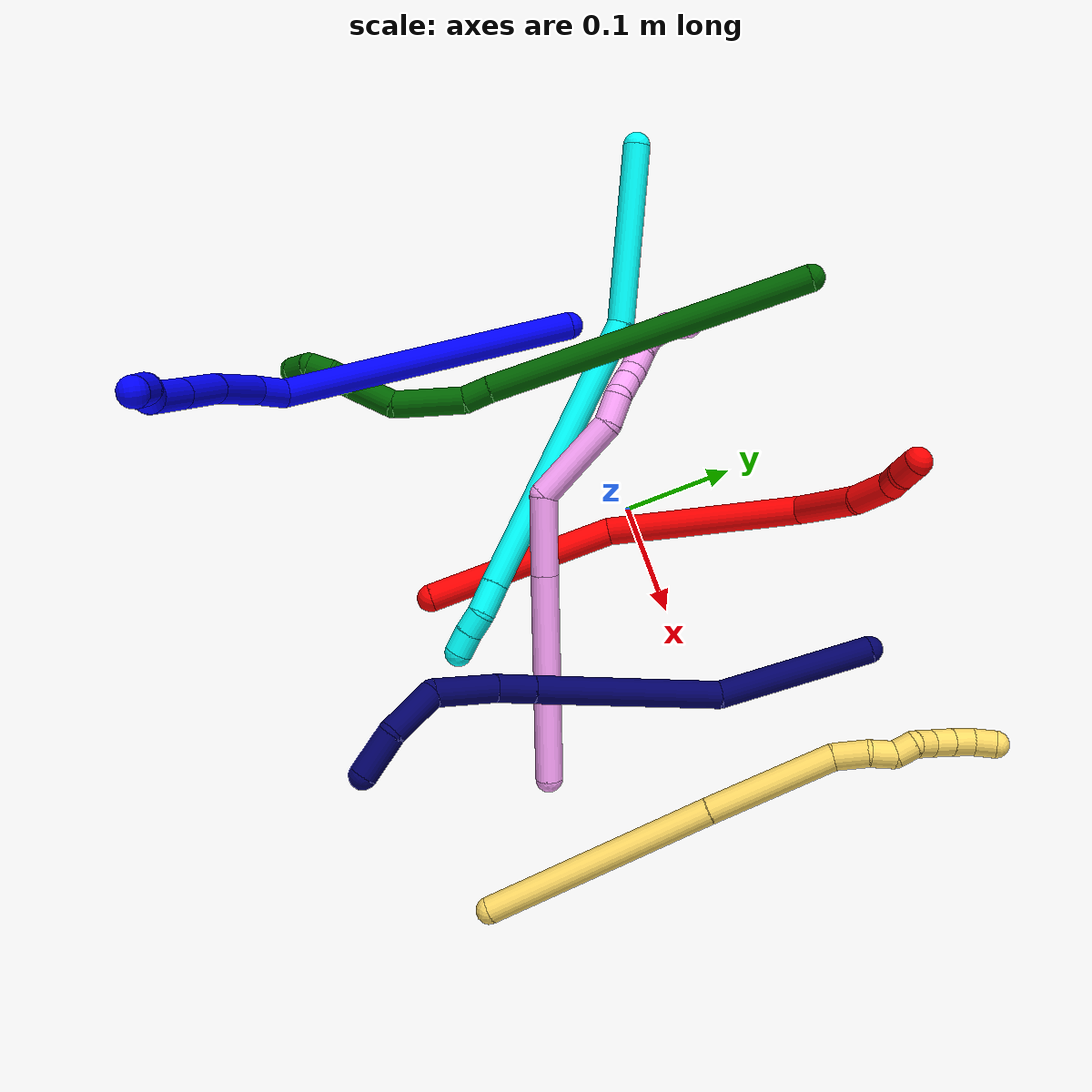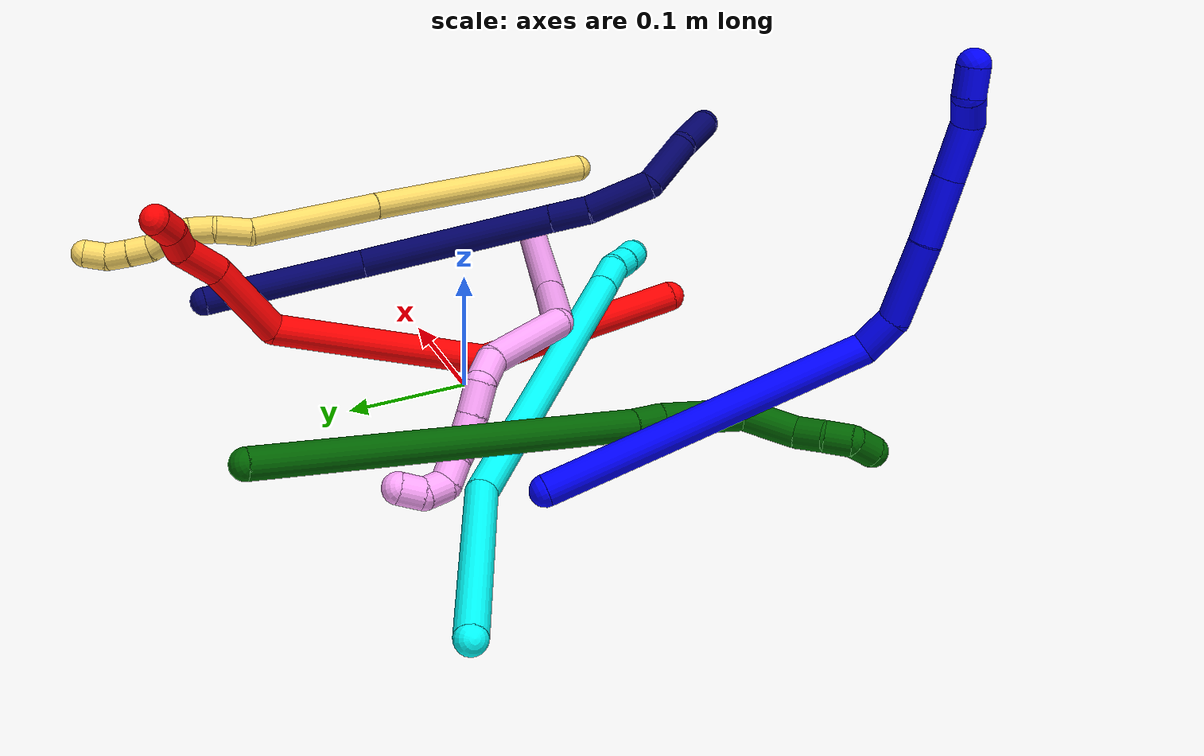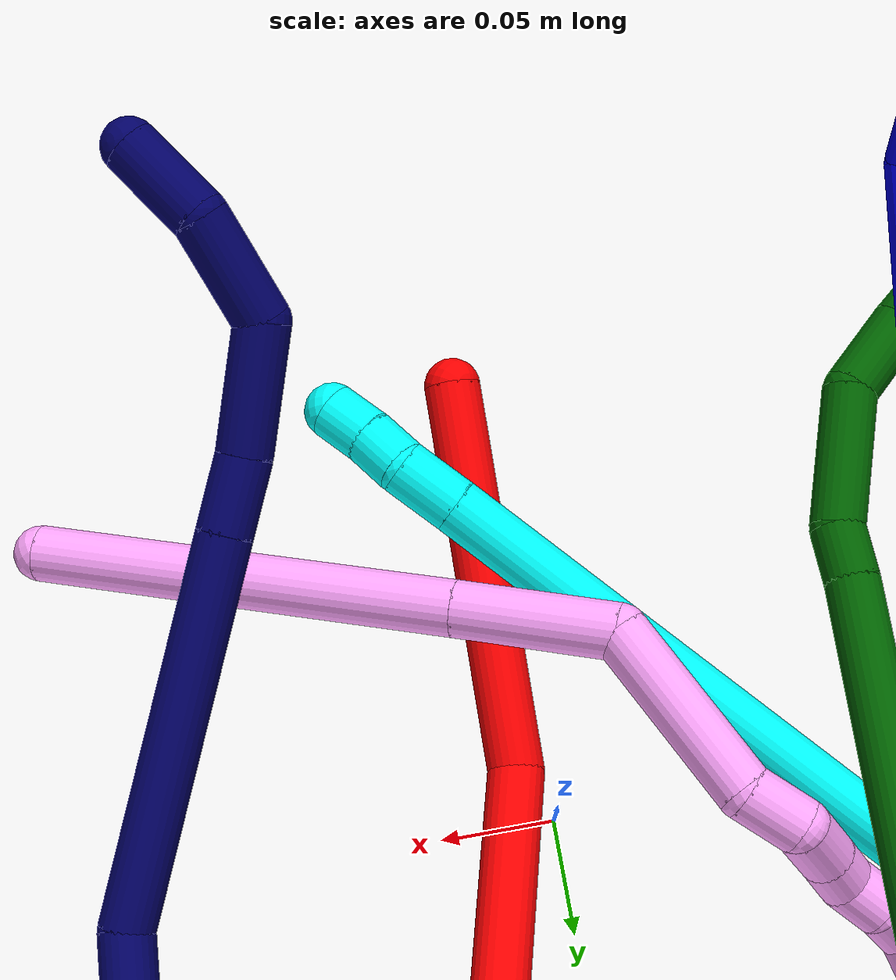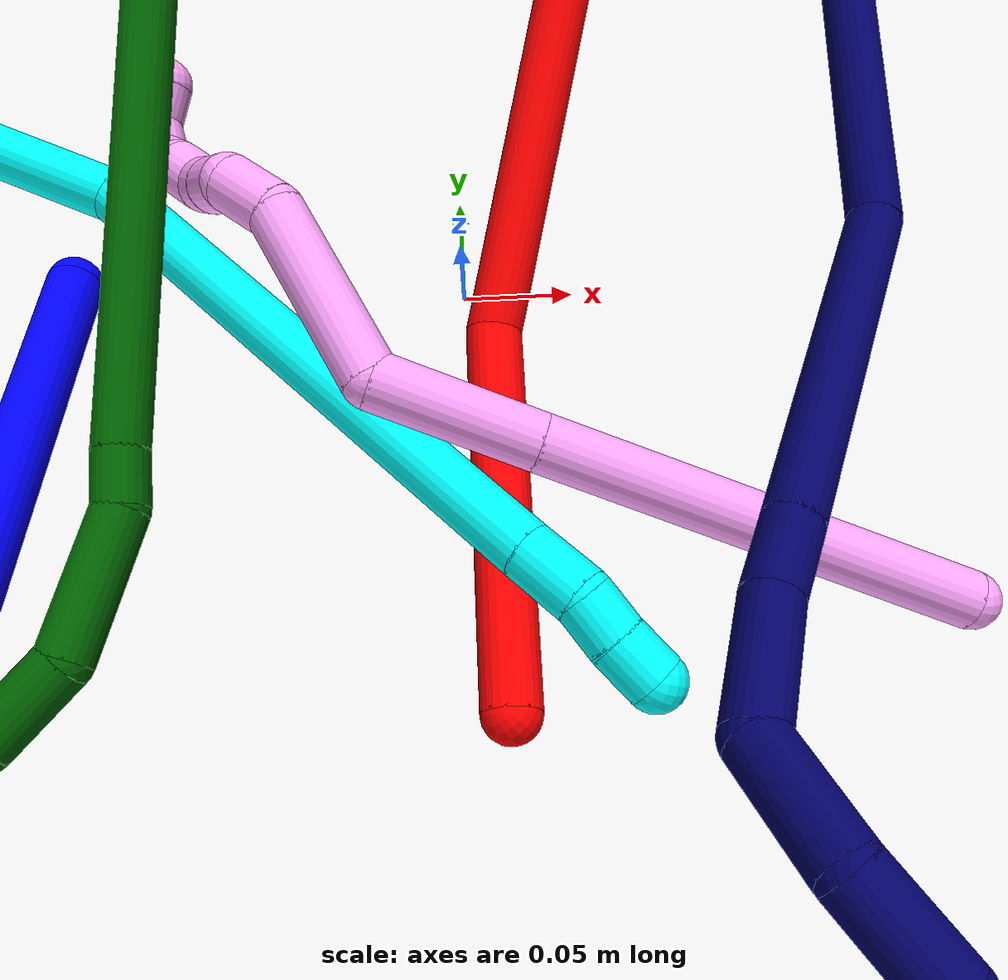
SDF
<sdf version="1.7">
 <world name="default">
  <plugin name="TubeGeneratorPlugin" filename="libtube_generator_plugin.so"/>
  <model name="photoneo_s_sensor">
   <static>1</static>
   <pose>0 0 2 1.57079 1.57079 3.14159</pose>
   <link name="link">
    <inertial><mass>0.1</mass></inertial>
    <sensor name="sensor" type="depth">
     <update_rate>30</update_rate>
     <camera>
      <horizontal_fov>1.22</horizontal_fov>
      <image><width>1920</width><height>1200</height><format>B8G8R8</format></image>
      <clip><near>0.1</near><far>4</far></clip>
      <depth_camera><output>points</output></depth_camera>
     </camera>
     <plugin name="camera_plugin" filename="libgazebo_ros_depth_camera.so">
      <baseline>0.2</baseline>
      <alwaysOn>1</alwaysOn>
      <updateRate>0.0</updateRate>
      <cameraName>camera_ir</cameraName>
      <imageTopicName>/camera/color/image_raw</imageTopicName>
      <cameraInfoTopicName>/camera/color/camera_info</cameraInfoTopicName>
      <depthImageTopicName>/camera/depth/image_raw</depthImageTopicName>
      <depthImageCameraInfoTopicName>/camera/depth/camera_info</depthImageCameraInfoTopicName>
      <pointCloudTopicName>/camera/depth/points</pointCloudTopicName>
      <frameName>fr_optical</frameName>
      <pointCloudCutoff>0.1</pointCloudCutoff>
      <pointCloudCutoffMax>2.0</pointCloudCutoffMax>
      <distortionK1>0</distortionK1>
      <distortionK2>0</distortionK2>
      <distortionK3>0</distortionK3>
      <distortionT1>0</distortionT1>
      <distortionT2>0</distortionT2>
      <CxPrime>0</CxPrime>
      <Cx>0</Cx>
      <Cy>0</Cy>
      <focalLength>0</focalLength>
      <hackBaseline>0</hackBaseline>
     </plugin>
    </sensor>
   </link>
  </model>
  <gravity>0 0 -9.8</gravity>
  <magnetic_field>6e-06 2.3e-05 -4.2e-05</magnetic_field>
  <atmosphere type="adiabatic"/>
  <physics name="default_physics" default="0" type="ode">
   <max_step_size>0.003</max_step_size>
   <real_time_factor>1</real_time_factor>
   <real_time_update_rate>1000</real_time_update_rate>
   <max_contacts>10000</max_contacts>
   <ode>
    <solver>
     <type>quick</type>
     <iters>100</iters>
     <sor>1.3</sor>
     <use_dynamic_moi_rescaling>0</use_dynamic_moi_rescaling>
    </solver>
    <constraints>
     <contact_max_correcting_vel>0</contact_max_correcting_vel>
     <contact_surface_layer>0.001</contact_surface_layer>
     <cfm>0</cfm>
     <erp>0.2</erp>
    </constraints>
   </ode>
  </physics>
  <scene><ambient>0.4 0.4 0.4 1</ambient><background>0.7 0.7 0.7 1</background><shadows>0</shadows></scene>
  <audio><device>default</device></audio>
  <spherical_coordinates>
   <surface_model>EARTH_WGS84</surface_model>
   <latitude_deg>0</latitude_deg>
   <longitude_deg>0</longitude_deg>
   <elevation>0</elevation>
   <heading_deg>0</heading_deg>
  </spherical_coordinates>
  <model name="bin">
   <static>1</static>
   <link name="bottom">
    <collision name="collision-bottom">
     <pose>0 0 -0.01 0 -0 0</pose>
     <geometry><box><size>0.8 0.6 0.02</size></box></geometry>
     <surface>
      <friction><ode><mu>100</mu><mu2>100</mu2></ode></friction>
      <contact><collide_bitmask>65535</collide_bitmask></contact>
     </surface>
    </collision>
   </link>
   <link name="west_wall">
    <collision name="collision-west_wall">
     <pose>-0.41 0 0.1 0 -0 0</pose>
     <geometry><box><size>0.02 0.6 0.2</size></box></geometry>
     <surface>
      <friction><ode><mu>100</mu><mu2>100</mu2></ode></friction>
      <contact><collide_bitmask>65535</collide_bitmask></contact>
     </surface>
    </collision>
   </link>
   <link name="east_wall">
    <collision name="collision-east_wall">
     <pose>0.41 0 0.1 0 -0 0</pose>
     <geometry><box><size>0.02 0.6 0.2</size></box></geometry>
     <surface>
      <friction><ode><mu>100</mu><mu2>100</mu2></ode></friction>
      <contact><collide_bitmask>65535</collide_bitmask></contact>
     </surface>
    </collision>
   </link>
   <link name="south_wall">
    <collision name="collision-south_wall">
     <pose>0 -0.31 0.1 0 -0 0</pose>
     <geometry><box><size>0.8 0.02 0.2</size></box></geometry>
     <surface>
      <friction><ode><mu>100</mu><mu2>100</mu2></ode></friction>
      <contact><collide_bitmask>65535</collide_bitmask></contact>
     </surface>
    </collision>
   </link>
   <link name="north_wall">
    <collision name="collision-north_wall">
     <pose>0 0.31 0.1 0 -0 0</pose>
     <geometry><box><size>0.8 0.02 0.2</size></box></geometry>
     <surface>
      <friction><ode><mu>100</mu><mu2>100</mu2></ode></friction>
      <contact><collide_bitmask>65535</collide_bitmask></contact>
     </surface>
    </collision>
   </link>
  </model>
  <model name="1">
   <static>0</static>
   <link name="1">
    <collision name="collision-cylinder-e_1_1_4">
     <pose>-0.019785 0.003382 0.131124 -0.025787 -0.149706 0.001934</pose>
     <geometry><cylinder><radius>0.0125</radius><length>0.265303</length></cylinder></geometry>
     <surface>
      <friction><ode><mu>1.16</mu><mu2>1.16</mu2><slip1>0</slip1><slip2>0</slip2></ode></friction>
      <contact><ode><kp>1e+06</kp><kd>1</kd><max_vel>0</max_vel><min_depth>0.001</min_depth></ode></contact>
     </surface>
    </collision>
    <visual name="visual-cylinder-e_1_1_4">
     <pose>-0.019785 0.003382 0.131124 -0.025787 -0.149706 0.001934</pose>
     <geometry><cylinder><radius>0.0125</radius><length>0.265303</length></cylinder></geometry>
     <material><ambient>0 0 1 1</ambient></material>
    </visual>
    <collision name="collision-cylinder-e_2_4_5">
     <pose>-0.032848 0.002767 0.27614 0.280189 0.435217 0.062341</pose>
     <geometry><cylinder><radius>0.0125</radius><length>0.031883</length></cylinder></geometry>
     <surface>
      <friction><ode><mu>1.16</mu><mu2>1.16</mu2><slip1>0</slip1><slip2>0</slip2></ode></friction>
      <contact><ode><kp>1e+06</kp><kd>1</kd><max_vel>0</max_vel><min_depth>0.001</min_depth></ode></contact>
     </surface>
    </collision>
    <visual name="visual-cylinder-e_2_4_5">
     <pose>-0.032848 0.002767 0.27614 0.280189 0.435217 0.062341</pose>
     <geometry><cylinder><radius>0.0125</radius><length>0.031883</length></cylinder></geometry>
     <material><ambient>0 0 1 1</ambient></material>
    </visual>
    <collision name="collision-cylinder-e_3_5_6">
     <pose>-0.009481 -0.019643 0.310573 0.730786 0.542935 0.21217</pose>
     <geometry><cylinder><radius>0.0125</radius><length>0.064437</length></cylinder></geometry>
     <surface>
      <friction><ode><mu>1.16</mu><mu2>1.16</mu2><slip1>0</slip1><slip2>0</slip2></ode></friction>
      <contact><ode><kp>1e+06</kp><kd>1</kd><max_vel>0</max_vel><min_depth>0.001</min_depth></ode></contact>
     </surface>
    </collision>
    <visual name="visual-cylinder-e_3_5_6">
     <pose>-0.009481 -0.019643 0.310573 0.730786 0.542935 0.21217</pose>
     <geometry><cylinder><radius>0.0125</radius><length>0.064437</length></cylinder></geometry>
     <material><ambient>0 0 1 1</ambient></material>
    </visual>
    <collision name="collision-cylinder-e_4_6_7">
     <pose>0.01834 -0.053978 0.347511 0.77076 0.454784 0.187188</pose>
     <geometry><cylinder><radius>0.0125</radius><length>0.050884</length></cylinder></geometry>
     <surface>
      <friction><ode><mu>1.16</mu><mu2>1.16</mu2><slip1>0</slip1><slip2>0</slip2></ode></friction>
      <contact><ode><kp>1e+06</kp><kd>1</kd><max_vel>0</max_vel><min_depth>0.001</min_depth></ode></contact>
     </surface>
    </collision>
    <visual name="visual-cylinder-e_4_6_7">
     <pose>0.01834 -0.053978 0.347511 0.77076 0.454784 0.187188</pose>
     <geometry><cylinder><radius>0.0125</radius><length>0.050884</length></cylinder></geometry>
     <material><ambient>0 0 1 1</ambient></material>
    </visual>
    <collision name="collision-cylinder-e_5_7_8">
     <pose>0.038908 -0.083073 0.377385 0.773901 0.462323 0.191238</pose>
     <geometry><cylinder><radius>0.0125</radius><length>0.042112</length></cylinder></geometry>
     <surface>
      <friction><ode><mu>1.16</mu><mu2>1.16</mu2><slip1>0</slip1><slip2>0</slip2></ode></friction>
      <contact><ode><kp>1e+06</kp><kd>1</kd><max_vel>0</max_vel><min_depth>0.001</min_depth></ode></contact>
     </surface>
    </collision>
    <visual name="visual-cylinder-e_5_7_8">
     <pose>0.038908 -0.083073 0.377385 0.773901 0.462323 0.191238</pose>
     <geometry><cylinder><radius>0.0125</radius><length>0.042112</length></cylinder></geometry>
     <material><ambient>0 0 1 1</ambient></material>
    </visual>
    <collision name="collision-cylinder-e_6_8_9">
     <pose>0.05748 -0.102741 0.39299 1.2544 0.930822 0.698217</pose>
     <geometry><cylinder><radius>0.0125</radius><length>0.022892</length></cylinder></geometry>
     <surface>
      <friction><ode><mu>1.16</mu><mu2>1.16</mu2><slip1>0</slip1><slip2>0</slip2></ode></friction>
      <contact><ode><kp>1e+06</kp><kd>1</kd><max_vel>0</max_vel><min_depth>0.001</min_depth></ode></contact>
     </surface>
    </collision>
    <visual name="visual-cylinder-e_6_8_9">
     <pose>0.05748 -0.102741 0.39299 1.2544 0.930822 0.698217</pose>
     <geometry><cylinder><radius>0.0125</radius><length>0.022892</length></cylinder></geometry>
     <material><ambient>0 0 1 1</ambient></material>
    </visual>
    <collision name="collision-cylinder-e_7_9_2">
     <pose>0.071925 -0.117484 0.400658 0.979176 0.487222 0.263349</pose>
     <geometry><cylinder><radius>0.0125</radius><length>0.02249</length></cylinder></geometry>
     <surface>
      <friction><ode><mu>1.16</mu><mu2>1.16</mu2><slip1>0</slip1><slip2>0</slip2></ode></friction>
      <contact><ode><kp>1e+06</kp><kd>1</kd><max_vel>0</max_vel><min_depth>0.001</min_depth></ode></contact>
     </surface>
    </collision>
    <visual name="visual-cylinder-e_7_9_2">
     <pose>0.071925 -0.117484 0.400658 0.979176 0.487222 0.263349</pose>
     <geometry><cylinder><radius>0.0125</radius><length>0.02249</length></cylinder></geometry>
     <material><ambient>0 0 1 1</ambient></material>
    </visual>
    <collision name="collision-sphere-2">
     <pose>0.07719 -0.125732 0.4062 0 -0 0</pose>
     <geometry><sphere><radius>0.0125</radius></sphere></geometry>
     <surface>
      <friction><ode><mu>1.16</mu><mu2>1.16</mu2><slip1>0</slip1><slip2>0</slip2></ode></friction>
      <contact><ode><kp>1e+06</kp><kd>1</kd><max_vel>0</max_vel><min_depth>0.001</min_depth></ode></contact>
     </surface>
    </collision>
    <visual name="visual-sphere-2">
     <pose>0.07719 -0.125732 0.4062 0 -0 0</pose>
     <geometry><sphere><radius>0.0125</radius></sphere></geometry>
     <material><ambient>0 0 1 1</ambient></material>
    </visual>
    <collision name="collision-sphere-9">
     <pose>0.066661 -0.109237 0.395117 0 -0 0</pose>
     <geometry><sphere><radius>0.0125</radius></sphere></geometry>
     <surface>
      <friction><ode><mu>1.16</mu><mu2>1.16</mu2><slip1>0</slip1><slip2>0</slip2></ode></friction>
      <contact><ode><kp>1e+06</kp><kd>1</kd><max_vel>0</max_vel><min_depth>0.001</min_depth></ode></contact>
     </surface>
    </collision>
    <visual name="visual-sphere-9">
     <pose>0.066661 -0.109237 0.395117 0 -0 0</pose>
     <geometry><sphere><radius>0.0125</radius></sphere></geometry>
     <material><ambient>0 0 1 1</ambient></material>
    </visual>
    <collision name="collision-sphere-4">
     <pose>-0.039569 0.006764 0.262248 0 -0 0</pose>
     <geometry><sphere><radius>0.0125</radius></sphere></geometry>
     <surface>
      <friction><ode><mu>1.16</mu><mu2>1.16</mu2><slip1>0</slip1><slip2>0</slip2></ode></friction>
      <contact><ode><kp>1e+06</kp><kd>1</kd><max_vel>0</max_vel><min_depth>0.001</min_depth></ode></contact>
     </surface>
    </collision>
    <visual name="visual-sphere-4">
     <pose>-0.039569 0.006764 0.262248 0 -0 0</pose>
     <geometry><sphere><radius>0.0125</radius></sphere></geometry>
     <material><ambient>0 0 1 1</ambient></material>
    </visual>
    <collision name="collision-sphere-1">
     <geometry><sphere><radius>0.0125</radius></sphere></geometry>
     <surface>
      <friction><ode><mu>1.16</mu><mu2>1.16</mu2><slip1>0</slip1><slip2>0</slip2></ode></friction>
      <contact><ode><kp>1e+06</kp><kd>1</kd><max_vel>0</max_vel><min_depth>0.001</min_depth></ode></contact>
     </surface>
    </collision>
    <visual name="visual-sphere-1">
     <geometry><sphere><radius>0.0125</radius></sphere></geometry>
     <material><ambient>0 0 1 1</ambient></material>
    </visual>
    <collision name="collision-sphere-8">
     <pose>0.048299 -0.096245 0.390863 0 -0 0</pose>
     <geometry><sphere><radius>0.0125</radius></sphere></geometry>
     <surface>
      <friction><ode><mu>1.16</mu><mu2>1.16</mu2><slip1>0</slip1><slip2>0</slip2></ode></friction>
      <contact><ode><kp>1e+06</kp><kd>1</kd><max_vel>0</max_vel><min_depth>0.001</min_depth></ode></contact>
     </surface>
    </collision>
    <visual name="visual-sphere-8">
     <pose>0.048299 -0.096245 0.390863 0 -0 0</pose>
     <geometry><sphere><radius>0.0125</radius></sphere></geometry>
     <material><ambient>0 0 1 1</ambient></material>
    </visual>
    <collision name="collision-sphere-5">
     <pose>-0.026127 -0.001231 0.290031 0 -0 0</pose>
     <geometry><sphere><radius>0.0125</radius></sphere></geometry>
     <surface>
      <friction><ode><mu>1.16</mu><mu2>1.16</mu2><slip1>0</slip1><slip2>0</slip2></ode></friction>
      <contact><ode><kp>1e+06</kp><kd>1</kd><max_vel>0</max_vel><min_depth>0.001</min_depth></ode></contact>
     </surface>
    </collision>
    <visual name="visual-sphere-5">
     <pose>-0.026127 -0.001231 0.290031 0 -0 0</pose>
     <geometry><sphere><radius>0.0125</radius></sphere></geometry>
     <material><ambient>0 0 1 1</ambient></material>
    </visual>
    <collision name="collision-sphere-6">
     <pose>0.007164 -0.038055 0.331114 0 -0 0</pose>
     <geometry><sphere><radius>0.0125</radius></sphere></geometry>
     <surface>
      <friction><ode><mu>1.16</mu><mu2>1.16</mu2><slip1>0</slip1><slip2>0</slip2></ode></friction>
      <contact><ode><kp>1e+06</kp><kd>1</kd><max_vel>0</max_vel><min_depth>0.001</min_depth></ode></contact>
     </surface>
    </collision>
    <visual name="visual-sphere-6">
     <pose>0.007164 -0.038055 0.331114 0 -0 0</pose>
     <geometry><sphere><radius>0.0125</radius></sphere></geometry>
     <material><ambient>0 0 1 1</ambient></material>
    </visual>
    <collision name="collision-sphere-7">
     <pose>0.029516 -0.069901 0.363907 0 -0 0</pose>
     <geometry><sphere><radius>0.0125</radius></sphere></geometry>
     <surface>
      <friction><ode><mu>1.16</mu><mu2>1.16</mu2><slip1>0</slip1><slip2>0</slip2></ode></friction>
      <contact><ode><kp>1e+06</kp><kd>1</kd><max_vel>0</max_vel><min_depth>0.001</min_depth></ode></contact>
     </surface>
    </collision>
    <visual name="visual-sphere-7">
     <pose>0.029516 -0.069901 0.363907 0 -0 0</pose>
     <geometry><sphere><radius>0.0125</radius></sphere></geometry>
     <material><ambient>0 0 1 1</ambient></material>
    </visual>
    <inertial>
     <pose>-0.002804 -0.023039 0.230372 0 -0 0</pose>
     <mass>0.5</mass>
     <inertia>
      <ixx>0.001612</ixx>
      <ixy>0</ixy>
      <ixz>0</ixz>
      <iyy>0.001611</iyy>
      <iyz>0</iyz>
      <izz>0.00023</izz>
     </inertia>
    </inertial>
   </link>
   <pose>-0.176759 0.010857 0.011966 -1.02579 -0.696645 2.58673</pose>
  </model>
  <model name="2">
   <static>0</static>
   <link name="2">
    <collision name="collision-cylinder-e_1_1_4">
     <pose>0.029544 0.073517 -0.034599 -2.01067 0.348744 -0.541565</pose>
     <geometry><cylinder><radius>0.0125</radius><length>0.172913</length></cylinder></geometry>
     <surface>
      <friction><ode><mu>1.16</mu><mu2>1.16</mu2><slip1>0</slip1><slip2>0</slip2></ode></friction>
      <contact><ode><kp>1e+06</kp><kd>1</kd><max_vel>0</max_vel><min_depth>0.001</min_depth></ode></contact>
     </surface>
    </collision>
    <visual name="visual-cylinder-e_1_1_4">
     <pose>0.029544 0.073517 -0.034599 -2.01067 0.348744 -0.541565</pose>
     <geometry><cylinder><radius>0.0125</radius><length>0.172913</length></cylinder></geometry>
     <material><ambient>1 0 0 1</ambient></material>
    </visual>
    <collision name="collision-cylinder-e_2_4_5">
     <pose>0.050005 0.22415 -0.111488 -2.07241 -0.102897 0.173501</pose>
     <geometry><cylinder><radius>0.0125</radius><length>0.176836</length></cylinder></geometry>
     <surface>
      <friction><ode><mu>1.16</mu><mu2>1.16</mu2><slip1>0</slip1><slip2>0</slip2></ode></friction>
      <contact><ode><kp>1e+06</kp><kd>1</kd><max_vel>0</max_vel><min_depth>0.001</min_depth></ode></contact>
     </surface>
    </collision>
    <visual name="visual-cylinder-e_2_4_5">
     <pose>0.050005 0.22415 -0.111488 -2.07241 -0.102897 0.173501</pose>
     <geometry><cylinder><radius>0.0125</radius><length>0.176836</length></cylinder></geometry>
     <material><ambient>1 0 0 1</ambient></material>
    </visual>
    <collision name="collision-cylinder-e_3_5_6">
     <pose>0.021902 0.315458 -0.179932 -2.64438 -0.568767 1.71136</pose>
     <geometry><cylinder><radius>0.0125</radius><length>0.070633</length></cylinder></geometry>
     <surface>
      <friction><ode><mu>1.16</mu><mu2>1.16</mu2><slip1>0</slip1><slip2>0</slip2></ode></friction>
      <contact><ode><kp>1e+06</kp><kd>1</kd><max_vel>0</max_vel><min_depth>0.001</min_depth></ode></contact>
     </surface>
    </collision>
    <visual name="visual-cylinder-e_3_5_6">
     <pose>0.021902 0.315458 -0.179932 -2.64438 -0.568767 1.71136</pose>
     <geometry><cylinder><radius>0.0125</radius><length>0.070633</length></cylinder></geometry>
     <material><ambient>1 0 0 1</ambient></material>
    </visual>
    <collision name="collision-cylinder-e_4_6_7">
     <pose>-0.002468 0.338635 -0.221701 -2.61953 -0.288637 0.996525</pose>
     <geometry><cylinder><radius>0.0125</radius><length>0.037584</length></cylinder></geometry>
     <surface>
      <friction><ode><mu>1.16</mu><mu2>1.16</mu2><slip1>0</slip1><slip2>0</slip2></ode></friction>
      <contact><ode><kp>1e+06</kp><kd>1</kd><max_vel>0</max_vel><min_depth>0.001</min_depth></ode></contact>
     </surface>
    </collision>
    <visual name="visual-cylinder-e_4_6_7">
     <pose>-0.002468 0.338635 -0.221701 -2.61953 -0.288637 0.996525</pose>
     <geometry><cylinder><radius>0.0125</radius><length>0.037584</length></cylinder></geometry>
     <material><ambient>1 0 0 1</ambient></material>
    </visual>
    <collision name="collision-cylinder-e_5_7_8">
     <pose>-0.01278 0.347723 -0.246813 -3.13057 -0.481511 3.09672</pose>
     <geometry><cylinder><radius>0.0125</radius><length>0.021433</length></cylinder></geometry>
     <surface>
      <friction><ode><mu>1.16</mu><mu2>1.16</mu2><slip1>0</slip1><slip2>0</slip2></ode></friction>
      <contact><ode><kp>1e+06</kp><kd>1</kd><max_vel>0</max_vel><min_depth>0.001</min_depth></ode></contact>
     </surface>
    </collision>
    <visual name="visual-cylinder-e_5_7_8">
     <pose>-0.01278 0.347723 -0.246813 -3.13057 -0.481511 3.09672</pose>
     <geometry><cylinder><radius>0.0125</radius><length>0.021433</length></cylinder></geometry>
     <material><ambient>1 0 0 1</ambient></material>
    </visual>
    <collision name="collision-cylinder-e_6_8_2">
     <pose>-0.020039 0.35043 -0.266009 -2.87937 -0.224765 1.41575</pose>
     <geometry><cylinder><radius>0.0125</radius><length>0.020601</length></cylinder></geometry>
     <surface>
      <friction><ode><mu>1.16</mu><mu2>1.16</mu2><slip1>0</slip1><slip2>0</slip2></ode></friction>
      <contact><ode><kp>1e+06</kp><kd>1</kd><max_vel>0</max_vel><min_depth>0.001</min_depth></ode></contact>
     </surface>
    </collision>
    <visual name="visual-cylinder-e_6_8_2">
     <pose>-0.020039 0.35043 -0.266009 -2.87937 -0.224765 1.41575</pose>
     <geometry><cylinder><radius>0.0125</radius><length>0.020601</length></cylinder></geometry>
     <material><ambient>1 0 0 1</ambient></material>
    </visual>
    <collision name="collision-sphere-2">
     <pose>-0.022335 0.353033 -0.275707 0 -0 0</pose>
     <geometry><sphere><radius>0.0125</radius></sphere></geometry>
     <surface>
      <friction><ode><mu>1.16</mu><mu2>1.16</mu2><slip1>0</slip1><slip2>0</slip2></ode></friction>
      <contact><ode><kp>1e+06</kp><kd>1</kd><max_vel>0</max_vel><min_depth>0.001</min_depth></ode></contact>
     </surface>
    </collision>
    <visual name="visual-sphere-2">
     <pose>-0.022335 0.353033 -0.275707 0 -0 0</pose>
     <geometry><sphere><radius>0.0125</radius></sphere></geometry>
     <material><ambient>1 0 0 1</ambient></material>
    </visual>
    <collision name="collision-sphere-4">
     <pose>0.059087 0.147034 -0.069198 0 -0 0</pose>
     <geometry><sphere><radius>0.0125</radius></sphere></geometry>
     <surface>
      <friction><ode><mu>1.16</mu><mu2>1.16</mu2><slip1>0</slip1><slip2>0</slip2></ode></friction>
      <contact><ode><kp>1e+06</kp><kd>1</kd><max_vel>0</max_vel><min_depth>0.001</min_depth></ode></contact>
     </surface>
    </collision>
    <visual name="visual-sphere-4">
     <pose>0.059087 0.147034 -0.069198 0 -0 0</pose>
     <geometry><sphere><radius>0.0125</radius></sphere></geometry>
     <material><ambient>1 0 0 1</ambient></material>
    </visual>
    <collision name="collision-sphere-1">
     <geometry><sphere><radius>0.0125</radius></sphere></geometry>
     <surface>
      <friction><ode><mu>1.16</mu><mu2>1.16</mu2><slip1>0</slip1><slip2>0</slip2></ode></friction>
      <contact><ode><kp>1e+06</kp><kd>1</kd><max_vel>0</max_vel><min_depth>0.001</min_depth></ode></contact>
     </surface>
    </collision>
    <visual name="visual-sphere-1">
     <geometry><sphere><radius>0.0125</radius></sphere></geometry>
     <material><ambient>1 0 0 1</ambient></material>
    </visual>
    <collision name="collision-sphere-8">
     <pose>-0.017744 0.347827 -0.256311 0 -0 0</pose>
     <geometry><sphere><radius>0.0125</radius></sphere></geometry>
     <surface>
      <friction><ode><mu>1.16</mu><mu2>1.16</mu2><slip1>0</slip1><slip2>0</slip2></ode></friction>
      <contact><ode><kp>1e+06</kp><kd>1</kd><max_vel>0</max_vel><min_depth>0.001</min_depth></ode></contact>
     </surface>
    </collision>
    <visual name="visual-sphere-8">
     <pose>-0.017744 0.347827 -0.256311 0 -0 0</pose>
     <geometry><sphere><radius>0.0125</radius></sphere></geometry>
     <material><ambient>1 0 0 1</ambient></material>
    </visual>
    <collision name="collision-sphere-5">
     <pose>0.040923 0.301265 -0.153779 0 -0 0</pose>
     <geometry><sphere><radius>0.0125</radius></sphere></geometry>
     <surface>
      <friction><ode><mu>1.16</mu><mu2>1.16</mu2><slip1>0</slip1><slip2>0</slip2></ode></friction>
      <contact><ode><kp>1e+06</kp><kd>1</kd><max_vel>0</max_vel><min_depth>0.001</min_depth></ode></contact>
     </surface>
    </collision>
    <visual name="visual-sphere-5">
     <pose>0.040923 0.301265 -0.153779 0 -0 0</pose>
     <geometry><sphere><radius>0.0125</radius></sphere></geometry>
     <material><ambient>1 0 0 1</ambient></material>
    </visual>
    <collision name="collision-sphere-6">
     <pose>0.002881 0.329651 -0.206086 0 -0 0</pose>
     <geometry><sphere><radius>0.0125</radius></sphere></geometry>
     <surface>
      <friction><ode><mu>1.16</mu><mu2>1.16</mu2><slip1>0</slip1><slip2>0</slip2></ode></friction>
      <contact><ode><kp>1e+06</kp><kd>1</kd><max_vel>0</max_vel><min_depth>0.001</min_depth></ode></contact>
     </surface>
    </collision>
    <visual name="visual-sphere-6">
     <pose>0.002881 0.329651 -0.206086 0 -0 0</pose>
     <geometry><sphere><radius>0.0125</radius></sphere></geometry>
     <material><ambient>1 0 0 1</ambient></material>
    </visual>
    <collision name="collision-sphere-7">
     <pose>-0.007817 0.347618 -0.237316 0 -0 0</pose>
     <geometry><sphere><radius>0.0125</radius></sphere></geometry>
     <surface>
      <friction><ode><mu>1.16</mu><mu2>1.16</mu2><slip1>0</slip1><slip2>0</slip2></ode></friction>
      <contact><ode><kp>1e+06</kp><kd>1</kd><max_vel>0</max_vel><min_depth>0.001</min_depth></ode></contact>
     </surface>
    </collision>
    <visual name="visual-sphere-7">
     <pose>-0.007817 0.347618 -0.237316 0 -0 0</pose>
     <geometry><sphere><radius>0.0125</radius></sphere></geometry>
     <material><ambient>1 0 0 1</ambient></material>
    </visual>
    <inertial>
     <pose>0.029437 0.204062 -0.115019 0 -0 0</pose>
     <mass>0.5</mass>
     <inertia>
      <ixx>0.000708</ixx>
      <ixy>0</ixy>
      <ixz>0</ixz>
      <iyy>-0.000364</iyy>
      <iyz>0</iyz>
      <izz>-0.000899</izz>
     </inertia>
    </inertial>
   </link>
   <pose>0.01106 -0.194379 0.033839 -2.9087 0.850028 2.74911</pose>
  </model>
  <model name="3">
   <static>0</static>
   <link name="3">
    <collision name="collision-cylinder-e_1_1_4">
     <pose>0.051144 -0.016386 -0.062534 2.88532 0.669323 2.43192</pose>
     <geometry><cylinder><radius>0.0125</radius><length>0.16486</length></cylinder></geometry>
     <surface>
      <friction><ode><mu>1.16</mu><mu2>1.16</mu2><slip1>0</slip1><slip2>0</slip2></ode></friction>
      <contact><ode><kp>1e+06</kp><kd>1</kd><max_vel>0</max_vel><min_depth>0.001</min_depth></ode></contact>
     </surface>
    </collision>
    <visual name="visual-cylinder-e_1_1_4">
     <pose>0.051144 -0.016386 -0.062534 2.88532 0.669323 2.43192</pose>
     <geometry><cylinder><radius>0.0125</radius><length>0.16486</length></cylinder></geometry>
     <material><ambient>0.003922 1 0.996078 1</ambient></material>
    </visual>
    <collision name="collision-cylinder-e_2_4_5">
     <pose>0.19457 -0.097241 -0.194976 2.39666 0.770374 1.60781</pose>
     <geometry><cylinder><radius>0.0125</radius><length>0.265023</length></cylinder></geometry>
     <surface>
      <friction><ode><mu>1.16</mu><mu2>1.16</mu2><slip1>0</slip1><slip2>0</slip2></ode></friction>
      <contact><ode><kp>1e+06</kp><kd>1</kd><max_vel>0</max_vel><min_depth>0.001</min_depth></ode></contact>
     </surface>
    </collision>
    <visual name="visual-cylinder-e_2_4_5">
     <pose>0.19457 -0.097241 -0.194976 2.39666 0.770374 1.60781</pose>
     <geometry><cylinder><radius>0.0125</radius><length>0.265023</length></cylinder></geometry>
     <material><ambient>0.003922 1 0.996078 1</ambient></material>
    </visual>
    <collision name="collision-cylinder-e_3_5_6">
     <pose>0.296975 -0.168474 -0.272615 2.42269 0.778148 1.65778</pose>
     <geometry><cylinder><radius>0.0125</radius><length>0.028845</length></cylinder></geometry>
     <surface>
      <friction><ode><mu>1.16</mu><mu2>1.16</mu2><slip1>0</slip1><slip2>0</slip2></ode></friction>
      <contact><ode><kp>1e+06</kp><kd>1</kd><max_vel>0</max_vel><min_depth>0.001</min_depth></ode></contact>
     </surface>
    </collision>
    <visual name="visual-cylinder-e_3_5_6">
     <pose>0.296975 -0.168474 -0.272615 2.42269 0.778148 1.65778</pose>
     <geometry><cylinder><radius>0.0125</radius><length>0.028845</length></cylinder></geometry>
     <material><ambient>0.003922 1 0.996078 1</ambient></material>
    </visual>
    <collision name="collision-cylinder-e_4_6_7">
     <pose>0.311557 -0.181892 -0.286589 2.32453 0.454447 0.981148</pose>
     <geometry><cylinder><radius>0.0125</radius><length>0.020309</length></cylinder></geometry>
     <surface>
      <friction><ode><mu>1.16</mu><mu2>1.16</mu2><slip1>0</slip1><slip2>0</slip2></ode></friction>
      <contact><ode><kp>1e+06</kp><kd>1</kd><max_vel>0</max_vel><min_depth>0.001</min_depth></ode></contact>
     </surface>
    </collision>
    <visual name="visual-cylinder-e_4_6_7">
     <pose>0.311557 -0.181892 -0.286589 2.32453 0.454447 0.981148</pose>
     <geometry><cylinder><radius>0.0125</radius><length>0.020309</length></cylinder></geometry>
     <material><ambient>0.003922 1 0.996078 1</ambient></material>
    </visual>
    <collision name="collision-cylinder-e_5_7_2">
     <pose>0.320925 -0.194551 -0.29988 2.43568 0.487629 1.1879</pose>
     <geometry><cylinder><radius>0.0125</radius><length>0.020963</length></cylinder></geometry>
     <surface>
      <friction><ode><mu>1.16</mu><mu2>1.16</mu2><slip1>0</slip1><slip2>0</slip2></ode></friction>
      <contact><ode><kp>1e+06</kp><kd>1</kd><max_vel>0</max_vel><min_depth>0.001</min_depth></ode></contact>
     </surface>
    </collision>
    <visual name="visual-cylinder-e_5_7_2">
     <pose>0.320925 -0.194551 -0.29988 2.43568 0.487629 1.1879</pose>
     <geometry><cylinder><radius>0.0125</radius><length>0.020963</length></cylinder></geometry>
     <material><ambient>0.003922 1 0.996078 1</ambient></material>
    </visual>
    <collision name="collision-sphere-2">
     <pose>0.325836 -0.200558 -0.306927 0 -0 0</pose>
     <geometry><sphere><radius>0.0125</radius></sphere></geometry>
     <surface>
      <friction><ode><mu>1.16</mu><mu2>1.16</mu2><slip1>0</slip1><slip2>0</slip2></ode></friction>
      <contact><ode><kp>1e+06</kp><kd>1</kd><max_vel>0</max_vel><min_depth>0.001</min_depth></ode></contact>
     </surface>
    </collision>
    <visual name="visual-sphere-2">
     <pose>0.325836 -0.200558 -0.306927 0 -0 0</pose>
     <geometry><sphere><radius>0.0125</radius></sphere></geometry>
     <material><ambient>0.003922 1 0.996078 1</ambient></material>
    </visual>
    <collision name="collision-sphere-7">
     <pose>0.316014 -0.188544 -0.292833 0 -0 0</pose>
     <geometry><sphere><radius>0.0125</radius></sphere></geometry>
     <surface>
      <friction><ode><mu>1.16</mu><mu2>1.16</mu2><slip1>0</slip1><slip2>0</slip2></ode></friction>
      <contact><ode><kp>1e+06</kp><kd>1</kd><max_vel>0</max_vel><min_depth>0.001</min_depth></ode></contact>
     </surface>
    </collision>
    <visual name="visual-sphere-7">
     <pose>0.316014 -0.188544 -0.292833 0 -0 0</pose>
     <geometry><sphere><radius>0.0125</radius></sphere></geometry>
     <material><ambient>0.003922 1 0.996078 1</ambient></material>
    </visual>
    <collision name="collision-sphere-6">
     <pose>0.307099 -0.175239 -0.280345 0 -0 0</pose>
     <geometry><sphere><radius>0.0125</radius></sphere></geometry>
     <surface>
      <friction><ode><mu>1.16</mu><mu2>1.16</mu2><slip1>0</slip1><slip2>0</slip2></ode></friction>
      <contact><ode><kp>1e+06</kp><kd>1</kd><max_vel>0</max_vel><min_depth>0.001</min_depth></ode></contact>
     </surface>
    </collision>
    <visual name="visual-sphere-6">
     <pose>0.307099 -0.175239 -0.280345 0 -0 0</pose>
     <geometry><sphere><radius>0.0125</radius></sphere></geometry>
     <material><ambient>0.003922 1 0.996078 1</ambient></material>
    </visual>
    <collision name="collision-sphere-5">
     <pose>0.286851 -0.16171 -0.264885 0 -0 0</pose>
     <geometry><sphere><radius>0.0125</radius></sphere></geometry>
     <surface>
      <friction><ode><mu>1.16</mu><mu2>1.16</mu2><slip1>0</slip1><slip2>0</slip2></ode></friction>
      <contact><ode><kp>1e+06</kp><kd>1</kd><max_vel>0</max_vel><min_depth>0.001</min_depth></ode></contact>
     </surface>
    </collision>
    <visual name="visual-sphere-5">
     <pose>0.286851 -0.16171 -0.264885 0 -0 0</pose>
     <geometry><sphere><radius>0.0125</radius></sphere></geometry>
     <material><ambient>0.003922 1 0.996078 1</ambient></material>
    </visual>
    <collision name="collision-sphere-1">
     <geometry><sphere><radius>0.0125</radius></sphere></geometry>
     <surface>
      <friction><ode><mu>1.16</mu><mu2>1.16</mu2><slip1>0</slip1><slip2>0</slip2></ode></friction>
      <contact><ode><kp>1e+06</kp><kd>1</kd><max_vel>0</max_vel><min_depth>0.001</min_depth></ode></contact>
     </surface>
    </collision>
    <visual name="visual-sphere-1">
     <geometry><sphere><radius>0.0125</radius></sphere></geometry>
     <material><ambient>0.003922 1 0.996078 1</ambient></material>
    </visual>
    <collision name="collision-sphere-4">
     <pose>0.102288 -0.032773 -0.125067 0 -0 0</pose>
     <geometry><sphere><radius>0.0125</radius></sphere></geometry>
     <surface>
      <friction><ode><mu>1.16</mu><mu2>1.16</mu2><slip1>0</slip1><slip2>0</slip2></ode></friction>
      <contact><ode><kp>1e+06</kp><kd>1</kd><max_vel>0</max_vel><min_depth>0.001</min_depth></ode></contact>
     </surface>
    </collision>
    <visual name="visual-sphere-4">
     <pose>0.102288 -0.032773 -0.125067 0 -0 0</pose>
     <geometry><sphere><radius>0.0125</radius></sphere></geometry>
     <material><ambient>0.003922 1 0.996078 1</ambient></material>
    </visual>
    <inertial>
     <pose>0.163237 -0.082209 -0.163906 0 -0 0</pose>
     <mass>0.5</mass>
     <inertia>
      <ixx>0.001078</ixx>
      <ixy>0</ixy>
      <ixz>0</ixz>
      <iyy>0.002401</iyy>
      <iyz>0</iyz>
      <izz>-0.000512</izz>
     </inertia>
    </inertial>
   </link>
   <pose>-0.308841 0.128097 0.011555 0.327067 -0.906906 -0.511739</pose>
  </model>
  <model name="4">
   <static>0</static>
   <link name="4">
    <collision name="collision-cylinder-e_1_1_4">
     <pose>-0.05752 0.029003 0.070895 -0.388327 -0.644101 0.131037</pose>
     <geometry><cylinder><radius>0.0125</radius><length>0.191582</length></cylinder></geometry>
     <surface>
      <friction><ode><mu>1.16</mu><mu2>1.16</mu2><slip1>0</slip1><slip2>0</slip2></ode></friction>
      <contact><ode><kp>1e+06</kp><kd>1</kd><max_vel>0</max_vel><min_depth>0.001</min_depth></ode></contact>
     </surface>
    </collision>
    <visual name="visual-cylinder-e_1_1_4">
     <pose>-0.05752 0.029003 0.070895 -0.388327 -0.644101 0.131037</pose>
     <geometry><cylinder><radius>0.0125</radius><length>0.191582</length></cylinder></geometry>
     <material><ambient>1 0.65098 0.996078 1</ambient></material>
    </visual>
    <collision name="collision-cylinder-e_2_4_5">
     <pose>-0.136688 0.06893 0.168006 -0.394801 -0.651255 0.134857</pose>
     <geometry><cylinder><radius>0.0125</radius><length>0.071421</length></cylinder></geometry>
     <surface>
      <friction><ode><mu>1.16</mu><mu2>1.16</mu2><slip1>0</slip1><slip2>0</slip2></ode></friction>
      <contact><ode><kp>1e+06</kp><kd>1</kd><max_vel>0</max_vel><min_depth>0.001</min_depth></ode></contact>
     </surface>
    </collision>
    <visual name="visual-cylinder-e_2_4_5">
     <pose>-0.136688 0.06893 0.168006 -0.394801 -0.651255 0.134857</pose>
     <geometry><cylinder><radius>0.0125</radius><length>0.071421</length></cylinder></geometry>
     <material><ambient>1 0.65098 0.996078 1</ambient></material>
    </visual>
    <collision name="collision-cylinder-e_3_5_6">
     <pose>-0.183112 0.11282 0.20162 -1.35006 -0.632771 0.512597</pose>
     <geometry><cylinder><radius>0.0125</radius><length>0.083794</length></cylinder></geometry>
     <surface>
      <friction><ode><mu>1.16</mu><mu2>1.16</mu2><slip1>0</slip1><slip2>0</slip2></ode></friction>
      <contact><ode><kp>1e+06</kp><kd>1</kd><max_vel>0</max_vel><min_depth>0.001</min_depth></ode></contact>
     </surface>
    </collision>
    <visual name="visual-cylinder-e_3_5_6">
     <pose>-0.183112 0.11282 0.20162 -1.35006 -0.632771 0.512597</pose>
     <geometry><cylinder><radius>0.0125</radius><length>0.083794</length></cylinder></geometry>
     <material><ambient>1 0.65098 0.996078 1</ambient></material>
    </visual>
    <collision name="collision-cylinder-e_4_6_7">
     <pose>-0.219328 0.151917 0.213352 -0.955456 -0.989885 0.544987</pose>
     <geometry><cylinder><radius>0.0125</radius><length>0.027366</length></cylinder></geometry>
     <surface>
      <friction><ode><mu>1.16</mu><mu2>1.16</mu2><slip1>0</slip1><slip2>0</slip2></ode></friction>
      <contact><ode><kp>1e+06</kp><kd>1</kd><max_vel>0</max_vel><min_depth>0.001</min_depth></ode></contact>
     </surface>
    </collision>
    <visual name="visual-cylinder-e_4_6_7">
     <pose>-0.219328 0.151917 0.213352 -0.955456 -0.989885 0.544987</pose>
     <geometry><cylinder><radius>0.0125</radius><length>0.027366</length></cylinder></geometry>
     <material><ambient>1 0.65098 0.996078 1</ambient></material>
    </visual>
    <collision name="collision-cylinder-e_5_7_8">
     <pose>-0.243219 0.158774 0.214367 -2.92647 -1.30444 2.86068</pose>
     <geometry><cylinder><radius>0.0125</radius><length>0.025816</length></cylinder></geometry>
     <surface>
      <friction><ode><mu>1.16</mu><mu2>1.16</mu2><slip1>0</slip1><slip2>0</slip2></ode></friction>
      <contact><ode><kp>1e+06</kp><kd>1</kd><max_vel>0</max_vel><min_depth>0.001</min_depth></ode></contact>
     </surface>
    </collision>
    <visual name="visual-cylinder-e_5_7_8">
     <pose>-0.243219 0.158774 0.214367 -2.92647 -1.30444 2.86068</pose>
     <geometry><cylinder><radius>0.0125</radius><length>0.025816</length></cylinder></geometry>
     <material><ambient>1 0.65098 0.996078 1</ambient></material>
    </visual>
    <collision name="collision-cylinder-e_6_8_9">
     <pose>-0.265279 0.16061 0.208482 -2.733 -1.2876 2.60285</pose>
     <geometry><cylinder><radius>0.0125</radius><length>0.020012</length></cylinder></geometry>
     <surface>
      <friction><ode><mu>1.16</mu><mu2>1.16</mu2><slip1>0</slip1><slip2>0</slip2></ode></friction>
      <contact><ode><kp>1e+06</kp><kd>1</kd><max_vel>0</max_vel><min_depth>0.001</min_depth></ode></contact>
     </surface>
    </collision>
    <visual name="visual-cylinder-e_6_8_9">
     <pose>-0.265279 0.16061 0.208482 -2.733 -1.2876 2.60285</pose>
     <geometry><cylinder><radius>0.0125</radius><length>0.020012</length></cylinder></geometry>
     <material><ambient>1 0.65098 0.996078 1</ambient></material>
    </visual>
    <collision name="collision-cylinder-e_7_9_10">
     <pose>-0.283641 0.166108 0.207966 -1.13367 -1.06547 0.718041</pose>
     <geometry><cylinder><radius>0.0125</radius><length>0.020009</length></cylinder></geometry>
     <surface>
      <friction><ode><mu>1.16</mu><mu2>1.16</mu2><slip1>0</slip1><slip2>0</slip2></ode></friction>
      <contact><ode><kp>1e+06</kp><kd>1</kd><max_vel>0</max_vel><min_depth>0.001</min_depth></ode></contact>
     </surface>
    </collision>
    <visual name="visual-cylinder-e_7_9_10">
     <pose>-0.283641 0.166108 0.207966 -1.13367 -1.06547 0.718041</pose>
     <geometry><cylinder><radius>0.0125</radius><length>0.020009</length></cylinder></geometry>
     <material><ambient>1 0.65098 0.996078 1</ambient></material>
    </visual>
    <collision name="collision-cylinder-e_8_10_11">
     <pose>-0.302029 0.173048 0.209202 -1.87968 -1.2996 1.61011</pose>
     <geometry><cylinder><radius>0.0125</radius><length>0.02</length></cylinder></geometry>
     <surface>
      <friction><ode><mu>1.16</mu><mu2>1.16</mu2><slip1>0</slip1><slip2>0</slip2></ode></friction>
      <contact><ode><kp>1e+06</kp><kd>1</kd><max_vel>0</max_vel><min_depth>0.001</min_depth></ode></contact>
     </surface>
    </collision>
    <visual name="visual-cylinder-e_8_10_11">
     <pose>-0.302029 0.173048 0.209202 -1.87968 -1.2996 1.61011</pose>
     <geometry><cylinder><radius>0.0125</radius><length>0.02</length></cylinder></geometry>
     <material><ambient>1 0.65098 0.996078 1</ambient></material>
    </visual>
    <collision name="collision-cylinder-e_9_11_12">
     <pose>-0.316745 0.184208 0.208077 -1.60688 -0.533016 0.551645</pose>
     <geometry><cylinder><radius>0.0125</radius><length>0.02</length></cylinder></geometry>
     <surface>
      <friction><ode><mu>1.16</mu><mu2>1.16</mu2><slip1>0</slip1><slip2>0</slip2></ode></friction>
      <contact><ode><kp>1e+06</kp><kd>1</kd><max_vel>0</max_vel><min_depth>0.001</min_depth></ode></contact>
     </surface>
    </collision>
    <visual name="visual-cylinder-e_9_11_12">
     <pose>-0.316745 0.184208 0.208077 -1.60688 -0.533016 0.551645</pose>
     <geometry><cylinder><radius>0.0125</radius><length>0.02</length></cylinder></geometry>
     <material><ambient>1 0.65098 0.996078 1</ambient></material>
    </visual>
    <collision name="collision-cylinder-e_10_12_2">
     <pose>-0.321059 0.20252 0.205481 -1.80207 0.076853 -0.097024</pose>
     <geometry><cylinder><radius>0.0125</radius><length>0.02</length></cylinder></geometry>
     <surface>
      <friction><ode><mu>1.16</mu><mu2>1.16</mu2><slip1>0</slip1><slip2>0</slip2></ode></friction>
      <contact><ode><kp>1e+06</kp><kd>1</kd><max_vel>0</max_vel><min_depth>0.001</min_depth></ode></contact>
     </surface>
    </collision>
    <visual name="visual-cylinder-e_10_12_2">
     <pose>-0.321059 0.20252 0.205481 -1.80207 0.076853 -0.097024</pose>
     <geometry><cylinder><radius>0.0125</radius><length>0.02</length></cylinder></geometry>
     <material><ambient>1 0.65098 0.996078 1</ambient></material>
    </visual>
    <collision name="collision-sphere-2">
     <pose>-0.320291 0.212226 0.203196 0 -0 0</pose>
     <geometry><sphere><radius>0.0125</radius></sphere></geometry>
     <surface>
      <friction><ode><mu>1.16</mu><mu2>1.16</mu2><slip1>0</slip1><slip2>0</slip2></ode></friction>
      <contact><ode><kp>1e+06</kp><kd>1</kd><max_vel>0</max_vel><min_depth>0.001</min_depth></ode></contact>
     </surface>
    </collision>
    <visual name="visual-sphere-2">
     <pose>-0.320291 0.212226 0.203196 0 -0 0</pose>
     <geometry><sphere><radius>0.0125</radius></sphere></geometry>
     <material><ambient>1 0.65098 0.996078 1</ambient></material>
    </visual>
    <collision name="collision-sphere-12">
     <pose>-0.321827 0.192815 0.207766 0 -0 0</pose>
     <geometry><sphere><radius>0.0125</radius></sphere></geometry>
     <surface>
      <friction><ode><mu>1.16</mu><mu2>1.16</mu2><slip1>0</slip1><slip2>0</slip2></ode></friction>
      <contact><ode><kp>1e+06</kp><kd>1</kd><max_vel>0</max_vel><min_depth>0.001</min_depth></ode></contact>
     </surface>
    </collision>
    <visual name="visual-sphere-12">
     <pose>-0.321827 0.192815 0.207766 0 -0 0</pose>
     <geometry><sphere><radius>0.0125</radius></sphere></geometry>
     <material><ambient>1 0.65098 0.996078 1</ambient></material>
    </visual>
    <collision name="collision-sphere-11">
     <pose>-0.311664 0.175601 0.208388 0 -0 0</pose>
     <geometry><sphere><radius>0.0125</radius></sphere></geometry>
     <surface>
      <friction><ode><mu>1.16</mu><mu2>1.16</mu2><slip1>0</slip1><slip2>0</slip2></ode></friction>
      <contact><ode><kp>1e+06</kp><kd>1</kd><max_vel>0</max_vel><min_depth>0.001</min_depth></ode></contact>
     </surface>
    </collision>
    <visual name="visual-sphere-11">
     <pose>-0.311664 0.175601 0.208388 0 -0 0</pose>
     <geometry><sphere><radius>0.0125</radius></sphere></geometry>
     <material><ambient>1 0.65098 0.996078 1</ambient></material>
    </visual>
    <collision name="collision-sphere-10">
     <pose>-0.292395 0.170496 0.210017 0 -0 0</pose>
     <geometry><sphere><radius>0.0125</radius></sphere></geometry>
     <surface>
      <friction><ode><mu>1.16</mu><mu2>1.16</mu2><slip1>0</slip1><slip2>0</slip2></ode></friction>
      <contact><ode><kp>1e+06</kp><kd>1</kd><max_vel>0</max_vel><min_depth>0.001</min_depth></ode></contact>
     </surface>
    </collision>
    <visual name="visual-sphere-10">
     <pose>-0.292395 0.170496 0.210017 0 -0 0</pose>
     <geometry><sphere><radius>0.0125</radius></sphere></geometry>
     <material><ambient>1 0.65098 0.996078 1</ambient></material>
    </visual>
    <collision name="collision-sphere-9">
     <pose>-0.274886 0.161721 0.205916 0 -0 0</pose>
     <geometry><sphere><radius>0.0125</radius></sphere></geometry>
     <surface>
      <friction><ode><mu>1.16</mu><mu2>1.16</mu2><slip1>0</slip1><slip2>0</slip2></ode></friction>
      <contact><ode><kp>1e+06</kp><kd>1</kd><max_vel>0</max_vel><min_depth>0.001</min_depth></ode></contact>
     </surface>
    </collision>
    <visual name="visual-sphere-9">
     <pose>-0.274886 0.161721 0.205916 0 -0 0</pose>
     <geometry><sphere><radius>0.0125</radius></sphere></geometry>
     <material><ambient>1 0.65098 0.996078 1</ambient></material>
    </visual>
    <collision name="collision-sphere-4">
     <pose>-0.115041 0.058006 0.14179 0 -0 0</pose>
     <geometry><sphere><radius>0.0125</radius></sphere></geometry>
     <surface>
      <friction><ode><mu>1.16</mu><mu2>1.16</mu2><slip1>0</slip1><slip2>0</slip2></ode></friction>
      <contact><ode><kp>1e+06</kp><kd>1</kd><max_vel>0</max_vel><min_depth>0.001</min_depth></ode></contact>
     </surface>
    </collision>
    <visual name="visual-sphere-4">
     <pose>-0.115041 0.058006 0.14179 0 -0 0</pose>
     <geometry><sphere><radius>0.0125</radius></sphere></geometry>
     <material><ambient>1 0.65098 0.996078 1</ambient></material>
    </visual>
    <collision name="collision-sphere-1">
     <geometry><sphere><radius>0.0125</radius></sphere></geometry>
     <surface>
      <friction><ode><mu>1.16</mu><mu2>1.16</mu2><slip1>0</slip1><slip2>0</slip2></ode></friction>
      <contact><ode><kp>1e+06</kp><kd>1</kd><max_vel>0</max_vel><min_depth>0.001</min_depth></ode></contact>
     </surface>
    </collision>
    <visual name="visual-sphere-1">
     <geometry><sphere><radius>0.0125</radius></sphere></geometry>
     <material><ambient>1 0.65098 0.996078 1</ambient></material>
    </visual>
    <collision name="collision-sphere-8">
     <pose>-0.255671 0.159499 0.211048 0 -0 0</pose>
     <geometry><sphere><radius>0.0125</radius></sphere></geometry>
     <surface>
      <friction><ode><mu>1.16</mu><mu2>1.16</mu2><slip1>0</slip1><slip2>0</slip2></ode></friction>
      <contact><ode><kp>1e+06</kp><kd>1</kd><max_vel>0</max_vel><min_depth>0.001</min_depth></ode></contact>
     </surface>
    </collision>
    <visual name="visual-sphere-8">
     <pose>-0.255671 0.159499 0.211048 0 -0 0</pose>
     <geometry><sphere><radius>0.0125</radius></sphere></geometry>
     <material><ambient>1 0.65098 0.996078 1</ambient></material>
    </visual>
    <collision name="collision-sphere-5">
     <pose>-0.158335 0.079854 0.194223 0 -0 0</pose>
     <geometry><sphere><radius>0.0125</radius></sphere></geometry>
     <surface>
      <friction><ode><mu>1.16</mu><mu2>1.16</mu2><slip1>0</slip1><slip2>0</slip2></ode></friction>
      <contact><ode><kp>1e+06</kp><kd>1</kd><max_vel>0</max_vel><min_depth>0.001</min_depth></ode></contact>
     </surface>
    </collision>
    <visual name="visual-sphere-5">
     <pose>-0.158335 0.079854 0.194223 0 -0 0</pose>
     <geometry><sphere><radius>0.0125</radius></sphere></geometry>
     <material><ambient>1 0.65098 0.996078 1</ambient></material>
    </visual>
    <collision name="collision-sphere-6">
     <pose>-0.207889 0.145785 0.209017 0 -0 0</pose>
     <geometry><sphere><radius>0.0125</radius></sphere></geometry>
     <surface>
      <friction><ode><mu>1.16</mu><mu2>1.16</mu2><slip1>0</slip1><slip2>0</slip2></ode></friction>
      <contact><ode><kp>1e+06</kp><kd>1</kd><max_vel>0</max_vel><min_depth>0.001</min_depth></ode></contact>
     </surface>
    </collision>
    <visual name="visual-sphere-6">
     <pose>-0.207889 0.145785 0.209017 0 -0 0</pose>
     <geometry><sphere><radius>0.0125</radius></sphere></geometry>
     <material><ambient>1 0.65098 0.996078 1</ambient></material>
    </visual>
    <collision name="collision-sphere-7">
     <pose>-0.230766 0.158048 0.217686 0 -0 0</pose>
     <geometry><sphere><radius>0.0125</radius></sphere></geometry>
     <surface>
      <friction><ode><mu>1.16</mu><mu2>1.16</mu2><slip1>0</slip1><slip2>0</slip2></ode></friction>
      <contact><ode><kp>1e+06</kp><kd>1</kd><max_vel>0</max_vel><min_depth>0.001</min_depth></ode></contact>
     </surface>
    </collision>
    <visual name="visual-sphere-7">
     <pose>-0.230766 0.158048 0.217686 0 -0 0</pose>
     <geometry><sphere><radius>0.0125</radius></sphere></geometry>
     <material><ambient>1 0.65098 0.996078 1</ambient></material>
    </visual>
    <inertial>
     <pose>-0.156376 0.091846 0.149274 0 -0 0</pose>
     <mass>0.5</mass>
     <inertia><ixx>0.0006</ixx><ixy>0</ixy><ixz>0</ixz><iyy>0.000732</iyy><iyz>0</iyz><izz>0.000196</izz></inertia>
    </inertial>
   </link>
   <pose>0.204087 -0.155468 0.012459 0.586453 -0.717573 -0.516094</pose>
  </model>
  <model name="5">
   <static>0</static>
   <link name="5">
    <collision name="collision-cylinder-e_1_1_4">
     <pose>0.074329 0.047886 -0.064728 -2.50465 0.745466 -1.74054</pose>
     <geometry><cylinder><radius>0.0125</radius><length>0.219158</length></cylinder></geometry>
     <surface>
      <friction><ode><mu>1.16</mu><mu2>1.16</mu2><slip1>0</slip1><slip2>0</slip2></ode></friction>
      <contact><ode><kp>1e+06</kp><kd>1</kd><max_vel>0</max_vel><min_depth>0.001</min_depth></ode></contact>
     </surface>
    </collision>
    <visual name="visual-cylinder-e_1_1_4">
     <pose>0.074329 0.047886 -0.064728 -2.50465 0.745466 -1.74054</pose>
     <geometry><cylinder><radius>0.0125</radius><length>0.219158</length></cylinder></geometry>
     <material><ambient>1 0.858824 0.4 1</ambient></material>
    </visual>
    <collision name="collision-cylinder-e_2_4_5">
     <pose>0.189449 0.124649 -0.165294 -2.46334 0.725193 -1.64347</pose>
     <geometry><cylinder><radius>0.0125</radius><length>0.123</length></cylinder></geometry>
     <surface>
      <friction><ode><mu>1.16</mu><mu2>1.16</mu2><slip1>0</slip1><slip2>0</slip2></ode></friction>
      <contact><ode><kp>1e+06</kp><kd>1</kd><max_vel>0</max_vel><min_depth>0.001</min_depth></ode></contact>
     </surface>
    </collision>
    <visual name="visual-cylinder-e_2_4_5">
     <pose>0.189449 0.124649 -0.165294 -2.46334 0.725193 -1.64347</pose>
     <geometry><cylinder><radius>0.0125</radius><length>0.123</length></cylinder></geometry>
     <material><ambient>1 0.858824 0.4 1</ambient></material>
    </visual>
    <collision name="collision-cylinder-e_3_5_6">
     <pose>0.237025 0.160446 -0.214024 -2.64901 0.434123 -1.44021</pose>
     <geometry><cylinder><radius>0.0125</radius><length>0.032256</length></cylinder></geometry>
     <surface>
      <friction><ode><mu>1.16</mu><mu2>1.16</mu2><slip1>0</slip1><slip2>0</slip2></ode></friction>
      <contact><ode><kp>1e+06</kp><kd>1</kd><max_vel>0</max_vel><min_depth>0.001</min_depth></ode></contact>
     </surface>
    </collision>
    <visual name="visual-cylinder-e_3_5_6">
     <pose>0.237025 0.160446 -0.214024 -2.64901 0.434123 -1.44021</pose>
     <geometry><cylinder><radius>0.0125</radius><length>0.032256</length></cylinder></geometry>
     <material><ambient>1 0.858824 0.4 1</ambient></material>
    </visual>
    <collision name="collision-cylinder-e_4_6_7">
     <pose>0.246612 0.175358 -0.235014 -2.36278 0.24159 -0.575203</pose>
     <geometry><cylinder><radius>0.0125</radius><length>0.023435</length></cylinder></geometry>
     <surface>
      <friction><ode><mu>1.16</mu><mu2>1.16</mu2><slip1>0</slip1><slip2>0</slip2></ode></friction>
      <contact><ode><kp>1e+06</kp><kd>1</kd><max_vel>0</max_vel><min_depth>0.001</min_depth></ode></contact>
     </surface>
    </collision>
    <visual name="visual-cylinder-e_4_6_7">
     <pose>0.246612 0.175358 -0.235014 -2.36278 0.24159 -0.575203</pose>
     <geometry><cylinder><radius>0.0125</radius><length>0.023435</length></cylinder></geometry>
     <material><ambient>1 0.858824 0.4 1</ambient></material>
    </visual>
    <collision name="collision-cylinder-e_5_7_8">
     <pose>0.25657 0.188376 -0.248149 -2.35723 0.788171 -1.57618</pose>
     <geometry><cylinder><radius>0.0125</radius><length>0.020182</length></cylinder></geometry>
     <surface>
      <friction><ode><mu>1.16</mu><mu2>1.16</mu2><slip1>0</slip1><slip2>0</slip2></ode></friction>
      <contact><ode><kp>1e+06</kp><kd>1</kd><max_vel>0</max_vel><min_depth>0.001</min_depth></ode></contact>
     </surface>
    </collision>
    <visual name="visual-cylinder-e_5_7_8">
     <pose>0.25657 0.188376 -0.248149 -2.35723 0.788171 -1.57618</pose>
     <geometry><cylinder><radius>0.0125</radius><length>0.020182</length></cylinder></geometry>
     <material><ambient>1 0.858824 0.4 1</ambient></material>
    </visual>
    <collision name="collision-cylinder-e_6_8_9">
     <pose>0.266111 0.202845 -0.256055 -1.86583 0.237199 -0.318776</pose>
     <geometry><cylinder><radius>0.0125</radius><length>0.020308</length></cylinder></geometry>
     <surface>
      <friction><ode><mu>1.16</mu><mu2>1.16</mu2><slip1>0</slip1><slip2>0</slip2></ode></friction>
      <contact><ode><kp>1e+06</kp><kd>1</kd><max_vel>0</max_vel><min_depth>0.001</min_depth></ode></contact>
     </surface>
    </collision>
    <visual name="visual-cylinder-e_6_8_9">
     <pose>0.266111 0.202845 -0.256055 -1.86583 0.237199 -0.318776</pose>
     <geometry><cylinder><radius>0.0125</radius><length>0.020308</length></cylinder></geometry>
     <material><ambient>1 0.858824 0.4 1</ambient></material>
    </visual>
    <collision name="collision-cylinder-e_7_9_10">
     <pose>0.271912 0.22005 -0.264937 -2.22985 0.334715 -0.663618</pose>
     <geometry><cylinder><radius>0.0125</radius><length>0.02079</length></cylinder></geometry>
     <surface>
      <friction><ode><mu>1.16</mu><mu2>1.16</mu2><slip1>0</slip1><slip2>0</slip2></ode></friction>
      <contact><ode><kp>1e+06</kp><kd>1</kd><max_vel>0</max_vel><min_depth>0.001</min_depth></ode></contact>
     </surface>
    </collision>
    <visual name="visual-cylinder-e_7_9_10">
     <pose>0.271912 0.22005 -0.264937 -2.22985 0.334715 -0.663618</pose>
     <geometry><cylinder><radius>0.0125</radius><length>0.02079</length></cylinder></geometry>
     <material><ambient>1 0.858824 0.4 1</ambient></material>
    </visual>
    <collision name="collision-cylinder-e_8_10_11">
     <pose>0.278278 0.235321 -0.277228 -2.26718 0.292822 -0.611269</pose>
     <geometry><cylinder><radius>0.0125</radius><length>0.020448</length></cylinder></geometry>
     <surface>
      <friction><ode><mu>1.16</mu><mu2>1.16</mu2><slip1>0</slip1><slip2>0</slip2></ode></friction>
      <contact><ode><kp>1e+06</kp><kd>1</kd><max_vel>0</max_vel><min_depth>0.001</min_depth></ode></contact>
     </surface>
    </collision>
    <visual name="visual-cylinder-e_8_10_11">
     <pose>0.278278 0.235321 -0.277228 -2.26718 0.292822 -0.611269</pose>
     <geometry><cylinder><radius>0.0125</radius><length>0.020448</length></cylinder></geometry>
     <material><ambient>1 0.858824 0.4 1</ambient></material>
    </visual>
    <collision name="collision-cylinder-e_9_11_2">
     <pose>0.283519 0.247959 -0.292036 -2.60026 0.226118 -0.776823</pose>
     <geometry><cylinder><radius>0.0125</radius><length>0.020424</length></cylinder></geometry>
     <surface>
      <friction><ode><mu>1.16</mu><mu2>1.16</mu2><slip1>0</slip1><slip2>0</slip2></ode></friction>
      <contact><ode><kp>1e+06</kp><kd>1</kd><max_vel>0</max_vel><min_depth>0.001</min_depth></ode></contact>
     </surface>
    </collision>
    <visual name="visual-cylinder-e_9_11_2">
     <pose>0.283519 0.247959 -0.292036 -2.60026 0.226118 -0.776823</pose>
     <geometry><cylinder><radius>0.0125</radius><length>0.020424</length></cylinder></geometry>
     <material><ambient>1 0.858824 0.4 1</ambient></material>
    </visual>
    <collision name="collision-sphere-2">
     <pose>0.285808 0.253087 -0.300566 0 -0 0</pose>
     <geometry><sphere><radius>0.0125</radius></sphere></geometry>
     <surface>
      <friction><ode><mu>1.16</mu><mu2>1.16</mu2><slip1>0</slip1><slip2>0</slip2></ode></friction>
      <contact><ode><kp>1e+06</kp><kd>1</kd><max_vel>0</max_vel><min_depth>0.001</min_depth></ode></contact>
     </surface>
    </collision>
    <visual name="visual-sphere-2">
     <pose>0.285808 0.253087 -0.300566 0 -0 0</pose>
     <geometry><sphere><radius>0.0125</radius></sphere></geometry>
     <material><ambient>1 0.858824 0.4 1</ambient></material>
    </visual>
    <collision name="collision-sphere-11">
     <pose>0.281229 0.242831 -0.283507 0 -0 0</pose>
     <geometry><sphere><radius>0.0125</radius></sphere></geometry>
     <surface>
      <friction><ode><mu>1.16</mu><mu2>1.16</mu2><slip1>0</slip1><slip2>0</slip2></ode></friction>
      <contact><ode><kp>1e+06</kp><kd>1</kd><max_vel>0</max_vel><min_depth>0.001</min_depth></ode></contact>
     </surface>
    </collision>
    <visual name="visual-sphere-11">
     <pose>0.281229 0.242831 -0.283507 0 -0 0</pose>
     <geometry><sphere><radius>0.0125</radius></sphere></geometry>
     <material><ambient>1 0.858824 0.4 1</ambient></material>
    </visual>
    <collision name="collision-sphere-10">
     <pose>0.275326 0.227811 -0.270949 0 -0 0</pose>
     <geometry><sphere><radius>0.0125</radius></sphere></geometry>
     <surface>
      <friction><ode><mu>1.16</mu><mu2>1.16</mu2><slip1>0</slip1><slip2>0</slip2></ode></friction>
      <contact><ode><kp>1e+06</kp><kd>1</kd><max_vel>0</max_vel><min_depth>0.001</min_depth></ode></contact>
     </surface>
    </collision>
    <visual name="visual-sphere-10">
     <pose>0.275326 0.227811 -0.270949 0 -0 0</pose>
     <geometry><sphere><radius>0.0125</radius></sphere></geometry>
     <material><ambient>1 0.858824 0.4 1</ambient></material>
    </visual>
    <collision name="collision-sphere-9">
     <pose>0.268497 0.212288 -0.258925 0 -0 0</pose>
     <geometry><sphere><radius>0.0125</radius></sphere></geometry>
     <surface>
      <friction><ode><mu>1.16</mu><mu2>1.16</mu2><slip1>0</slip1><slip2>0</slip2></ode></friction>
      <contact><ode><kp>1e+06</kp><kd>1</kd><max_vel>0</max_vel><min_depth>0.001</min_depth></ode></contact>
     </surface>
    </collision>
    <visual name="visual-sphere-9">
     <pose>0.268497 0.212288 -0.258925 0 -0 0</pose>
     <geometry><sphere><radius>0.0125</radius></sphere></geometry>
     <material><ambient>1 0.858824 0.4 1</ambient></material>
    </visual>
    <collision name="collision-sphere-4">
     <pose>0.148658 0.095772 -0.129456 0 -0 0</pose>
     <geometry><sphere><radius>0.0125</radius></sphere></geometry>
     <surface>
      <friction><ode><mu>1.16</mu><mu2>1.16</mu2><slip1>0</slip1><slip2>0</slip2></ode></friction>
      <contact><ode><kp>1e+06</kp><kd>1</kd><max_vel>0</max_vel><min_depth>0.001</min_depth></ode></contact>
     </surface>
    </collision>
    <visual name="visual-sphere-4">
     <pose>0.148658 0.095772 -0.129456 0 -0 0</pose>
     <geometry><sphere><radius>0.0125</radius></sphere></geometry>
     <material><ambient>1 0.858824 0.4 1</ambient></material>
    </visual>
    <collision name="collision-sphere-1">
     <geometry><sphere><radius>0.0125</radius></sphere></geometry>
     <surface>
      <friction><ode><mu>1.16</mu><mu2>1.16</mu2><slip1>0</slip1><slip2>0</slip2></ode></friction>
      <contact><ode><kp>1e+06</kp><kd>1</kd><max_vel>0</max_vel><min_depth>0.001</min_depth></ode></contact>
     </surface>
    </collision>
    <visual name="visual-sphere-1">
     <geometry><sphere><radius>0.0125</radius></sphere></geometry>
     <material><ambient>1 0.858824 0.4 1</ambient></material>
    </visual>
    <collision name="collision-sphere-8">
     <pose>0.263725 0.193402 -0.253185 0 -0 0</pose>
     <geometry><sphere><radius>0.0125</radius></sphere></geometry>
     <surface>
      <friction><ode><mu>1.16</mu><mu2>1.16</mu2><slip1>0</slip1><slip2>0</slip2></ode></friction>
      <contact><ode><kp>1e+06</kp><kd>1</kd><max_vel>0</max_vel><min_depth>0.001</min_depth></ode></contact>
     </surface>
    </collision>
    <visual name="visual-sphere-8">
     <pose>0.263725 0.193402 -0.253185 0 -0 0</pose>
     <geometry><sphere><radius>0.0125</radius></sphere></geometry>
     <material><ambient>1 0.858824 0.4 1</ambient></material>
    </visual>
    <collision name="collision-sphere-5">
     <pose>0.230241 0.153527 -0.201132 0 -0 0</pose>
     <geometry><sphere><radius>0.0125</radius></sphere></geometry>
     <surface>
      <friction><ode><mu>1.16</mu><mu2>1.16</mu2><slip1>0</slip1><slip2>0</slip2></ode></friction>
      <contact><ode><kp>1e+06</kp><kd>1</kd><max_vel>0</max_vel><min_depth>0.001</min_depth></ode></contact>
     </surface>
    </collision>
    <visual name="visual-sphere-5">
     <pose>0.230241 0.153527 -0.201132 0 -0 0</pose>
     <geometry><sphere><radius>0.0125</radius></sphere></geometry>
     <material><ambient>1 0.858824 0.4 1</ambient></material>
    </visual>
    <collision name="collision-sphere-6">
     <pose>0.243808 0.167366 -0.226916 0 -0 0</pose>
     <geometry><sphere><radius>0.0125</radius></sphere></geometry>
     <surface>
      <friction><ode><mu>1.16</mu><mu2>1.16</mu2><slip1>0</slip1><slip2>0</slip2></ode></friction>
      <contact><ode><kp>1e+06</kp><kd>1</kd><max_vel>0</max_vel><min_depth>0.001</min_depth></ode></contact>
     </surface>
    </collision>
    <visual name="visual-sphere-6">
     <pose>0.243808 0.167366 -0.226916 0 -0 0</pose>
     <geometry><sphere><radius>0.0125</radius></sphere></geometry>
     <material><ambient>1 0.858824 0.4 1</ambient></material>
    </visual>
    <collision name="collision-sphere-7">
     <pose>0.249415 0.18335 -0.243112 0 -0 0</pose>
     <geometry><sphere><radius>0.0125</radius></sphere></geometry>
     <surface>
      <friction><ode><mu>1.16</mu><mu2>1.16</mu2><slip1>0</slip1><slip2>0</slip2></ode></friction>
      <contact><ode><kp>1e+06</kp><kd>1</kd><max_vel>0</max_vel><min_depth>0.001</min_depth></ode></contact>
     </surface>
    </collision>
    <visual name="visual-sphere-7">
     <pose>0.249415 0.18335 -0.243112 0 -0 0</pose>
     <geometry><sphere><radius>0.0125</radius></sphere></geometry>
     <material><ambient>1 0.858824 0.4 1</ambient></material>
    </visual>
    <inertial>
     <pose>0.161466 0.114967 -0.148554 0 -0 0</pose>
     <mass>0.5</mass>
     <inertia>
      <ixx>-0.000859</ixx>
      <ixy>0</ixy>
      <ixz>0</ixz>
      <iyy>-0.000204</iyy>
      <iyz>0</iyz>
      <izz>-0.001206</izz>
     </inertia>
    </inertial>
   </link>
   <pose>0.295366 -0.24842 0.01988 -2.26301 0.005678 2.45924</pose>
  </model>
  <model name="6">
   <static>0</static>
   <link name="6">
    <collision name="collision-cylinder-e_1_1_4">
     <pose>-0.031466 -0.138398 0.05395 1.1991 -0.208747 -0.14295</pose>
     <geometry><cylinder><radius>0.0125</radius><length>0.303675</length></cylinder></geometry>
     <surface>
      <friction><ode><mu>1.16</mu><mu2>1.16</mu2><slip1>0</slip1><slip2>0</slip2></ode></friction>
      <contact><ode><kp>1e+06</kp><kd>1</kd><max_vel>0</max_vel><min_depth>0.001</min_depth></ode></contact>
     </surface>
    </collision>
    <visual name="visual-cylinder-e_1_1_4">
     <pose>-0.031466 -0.138398 0.05395 1.1991 -0.208747 -0.14295</pose>
     <geometry><cylinder><radius>0.0125</radius><length>0.303675</length></cylinder></geometry>
     <material><ambient>0 0.392157 0.003922 1</ambient></material>
    </visual>
    <collision name="collision-cylinder-e_2_4_5">
     <pose>-0.06436 -0.288695 0.112079 1.23305 -0.11277 -0.07996</pose>
     <geometry><cylinder><radius>0.0125</radius><length>0.025385</length></cylinder></geometry>
     <surface>
      <friction><ode><mu>1.16</mu><mu2>1.16</mu2><slip1>0</slip1><slip2>0</slip2></ode></friction>
      <contact><ode><kp>1e+06</kp><kd>1</kd><max_vel>0</max_vel><min_depth>0.001</min_depth></ode></contact>
     </surface>
    </collision>
    <visual name="visual-cylinder-e_2_4_5">
     <pose>-0.06436 -0.288695 0.112079 1.23305 -0.11277 -0.07996</pose>
     <geometry><cylinder><radius>0.0125</radius><length>0.025385</length></cylinder></geometry>
     <material><ambient>0 0.392157 0.003922 1</ambient></material>
    </visual>
    <collision name="collision-cylinder-e_3_5_6">
     <pose>-0.073782 -0.325357 0.135407 0.912567 -0.250029 -0.123209</pose>
     <geometry><cylinder><radius>0.0125</radius><length>0.064613</length></cylinder></geometry>
     <surface>
      <friction><ode><mu>1.16</mu><mu2>1.16</mu2><slip1>0</slip1><slip2>0</slip2></ode></friction>
      <contact><ode><kp>1e+06</kp><kd>1</kd><max_vel>0</max_vel><min_depth>0.001</min_depth></ode></contact>
     </surface>
    </collision>
    <visual name="visual-cylinder-e_3_5_6">
     <pose>-0.073782 -0.325357 0.135407 0.912567 -0.250029 -0.123209</pose>
     <geometry><cylinder><radius>0.0125</radius><length>0.064613</length></cylinder></geometry>
     <material><ambient>0 0.392157 0.003922 1</ambient></material>
    </visual>
    <collision name="collision-cylinder-e_4_6_7">
     <pose>-0.093742 -0.358431 0.169904 0.496324 -0.600917 -0.156695</pose>
     <geometry><cylinder><radius>0.0125</radius><length>0.042327</length></cylinder></geometry>
     <surface>
      <friction><ode><mu>1.16</mu><mu2>1.16</mu2><slip1>0</slip1><slip2>0</slip2></ode></friction>
      <contact><ode><kp>1e+06</kp><kd>1</kd><max_vel>0</max_vel><min_depth>0.001</min_depth></ode></contact>
     </surface>
    </collision>
    <visual name="visual-cylinder-e_4_6_7">
     <pose>-0.093742 -0.358431 0.169904 0.496324 -0.600917 -0.156695</pose>
     <geometry><cylinder><radius>0.0125</radius><length>0.042327</length></cylinder></geometry>
     <material><ambient>0 0.392157 0.003922 1</ambient></material>
    </visual>
    <collision name="collision-cylinder-e_5_7_8">
     <pose>-0.109823 -0.369803 0.195071 0.302053 -0.380678 -0.058627</pose>
     <geometry><cylinder><radius>0.0125</radius><length>0.022151</length></cylinder></geometry>
     <surface>
      <friction><ode><mu>1.16</mu><mu2>1.16</mu2><slip1>0</slip1><slip2>0</slip2></ode></friction>
      <contact><ode><kp>1e+06</kp><kd>1</kd><max_vel>0</max_vel><min_depth>0.001</min_depth></ode></contact>
     </surface>
    </collision>
    <visual name="visual-cylinder-e_5_7_8">
     <pose>-0.109823 -0.369803 0.195071 0.302053 -0.380678 -0.058627</pose>
     <geometry><cylinder><radius>0.0125</radius><length>0.022151</length></cylinder></geometry>
     <material><ambient>0 0.392157 0.003922 1</ambient></material>
    </visual>
    <collision name="collision-cylinder-e_6_8_9">
     <pose>-0.118579 -0.378041 0.212948 0.571152 -0.45114 -0.134545</pose>
     <geometry><cylinder><radius>0.0125</radius><length>0.02129</length></cylinder></geometry>
     <surface>
      <friction><ode><mu>1.16</mu><mu2>1.16</mu2><slip1>0</slip1><slip2>0</slip2></ode></friction>
      <contact><ode><kp>1e+06</kp><kd>1</kd><max_vel>0</max_vel><min_depth>0.001</min_depth></ode></contact>
     </surface>
    </collision>
    <visual name="visual-cylinder-e_6_8_9">
     <pose>-0.118579 -0.378041 0.212948 0.571152 -0.45114 -0.134545</pose>
     <geometry><cylinder><radius>0.0125</radius><length>0.02129</length></cylinder></geometry>
     <material><ambient>0 0.392157 0.003922 1</ambient></material>
    </visual>
    <collision name="collision-cylinder-e_7_9_2">
     <pose>-0.129658 -0.391125 0.222319 1.4063 -0.676844 -0.579895</pose>
     <geometry><cylinder><radius>0.0125</radius><length>0.020558</length></cylinder></geometry>
     <surface>
      <friction><ode><mu>1.16</mu><mu2>1.16</mu2><slip1>0</slip1><slip2>0</slip2></ode></friction>
      <contact><ode><kp>1e+06</kp><kd>1</kd><max_vel>0</max_vel><min_depth>0.001</min_depth></ode></contact>
     </surface>
    </collision>
    <visual name="visual-cylinder-e_7_9_2">
     <pose>-0.129658 -0.391125 0.222319 1.4063 -0.676844 -0.579895</pose>
     <geometry><cylinder><radius>0.0125</radius><length>0.020558</length></cylinder></geometry>
     <material><ambient>0 0.392157 0.003922 1</ambient></material>
    </visual>
    <collision name="collision-sphere-2">
     <pose>-0.136097 -0.39903 0.223631 0 -0 0</pose>
     <geometry><sphere><radius>0.0125</radius></sphere></geometry>
     <surface>
      <friction><ode><mu>1.16</mu><mu2>1.16</mu2><slip1>0</slip1><slip2>0</slip2></ode></friction>
      <contact><ode><kp>1e+06</kp><kd>1</kd><max_vel>0</max_vel><min_depth>0.001</min_depth></ode></contact>
     </surface>
    </collision>
    <visual name="visual-sphere-2">
     <pose>-0.136097 -0.39903 0.223631 0 -0 0</pose>
     <geometry><sphere><radius>0.0125</radius></sphere></geometry>
     <material><ambient>0 0.392157 0.003922 1</ambient></material>
    </visual>
    <collision name="collision-sphere-9">
     <pose>-0.12322 -0.38322 0.221007 0 -0 0</pose>
     <geometry><sphere><radius>0.0125</radius></sphere></geometry>
     <surface>
      <friction><ode><mu>1.16</mu><mu2>1.16</mu2><slip1>0</slip1><slip2>0</slip2></ode></friction>
      <contact><ode><kp>1e+06</kp><kd>1</kd><max_vel>0</max_vel><min_depth>0.001</min_depth></ode></contact>
     </surface>
    </collision>
    <visual name="visual-sphere-9">
     <pose>-0.12322 -0.38322 0.221007 0 -0 0</pose>
     <geometry><sphere><radius>0.0125</radius></sphere></geometry>
     <material><ambient>0 0.392157 0.003922 1</ambient></material>
    </visual>
    <collision name="collision-sphere-4">
     <pose>-0.062932 -0.276795 0.1079 0 -0 0</pose>
     <geometry><sphere><radius>0.0125</radius></sphere></geometry>
     <surface>
      <friction><ode><mu>1.16</mu><mu2>1.16</mu2><slip1>0</slip1><slip2>0</slip2></ode></friction>
      <contact><ode><kp>1e+06</kp><kd>1</kd><max_vel>0</max_vel><min_depth>0.001</min_depth></ode></contact>
     </surface>
    </collision>
    <visual name="visual-sphere-4">
     <pose>-0.062932 -0.276795 0.1079 0 -0 0</pose>
     <geometry><sphere><radius>0.0125</radius></sphere></geometry>
     <material><ambient>0 0.392157 0.003922 1</ambient></material>
    </visual>
    <collision name="collision-sphere-1">
     <geometry><sphere><radius>0.0125</radius></sphere></geometry>
     <surface>
      <friction><ode><mu>1.16</mu><mu2>1.16</mu2><slip1>0</slip1><slip2>0</slip2></ode></friction>
      <contact><ode><kp>1e+06</kp><kd>1</kd><max_vel>0</max_vel><min_depth>0.001</min_depth></ode></contact>
     </surface>
    </collision>
    <visual name="visual-sphere-1">
     <geometry><sphere><radius>0.0125</radius></sphere></geometry>
     <material><ambient>0 0.392157 0.003922 1</ambient></material>
    </visual>
    <collision name="collision-sphere-8">
     <pose>-0.113938 -0.372862 0.204888 0 -0 0</pose>
     <geometry><sphere><radius>0.0125</radius></sphere></geometry>
     <surface>
      <friction><ode><mu>1.16</mu><mu2>1.16</mu2><slip1>0</slip1><slip2>0</slip2></ode></friction>
      <contact><ode><kp>1e+06</kp><kd>1</kd><max_vel>0</max_vel><min_depth>0.001</min_depth></ode></contact>
     </surface>
    </collision>
    <visual name="visual-sphere-8">
     <pose>-0.113938 -0.372862 0.204888 0 -0 0</pose>
     <geometry><sphere><radius>0.0125</radius></sphere></geometry>
     <material><ambient>0 0.392157 0.003922 1</ambient></material>
    </visual>
    <collision name="collision-sphere-5">
     <pose>-0.065789 -0.300594 0.116259 0 -0 0</pose>
     <geometry><sphere><radius>0.0125</radius></sphere></geometry>
     <surface>
      <friction><ode><mu>1.16</mu><mu2>1.16</mu2><slip1>0</slip1><slip2>0</slip2></ode></friction>
      <contact><ode><kp>1e+06</kp><kd>1</kd><max_vel>0</max_vel><min_depth>0.001</min_depth></ode></contact>
     </surface>
    </collision>
    <visual name="visual-sphere-5">
     <pose>-0.065789 -0.300594 0.116259 0 -0 0</pose>
     <geometry><sphere><radius>0.0125</radius></sphere></geometry>
     <material><ambient>0 0.392157 0.003922 1</ambient></material>
    </visual>
    <collision name="collision-sphere-6">
     <pose>-0.081776 -0.350119 0.154555 0 -0 0</pose>
     <geometry><sphere><radius>0.0125</radius></sphere></geometry>
     <surface>
      <friction><ode><mu>1.16</mu><mu2>1.16</mu2><slip1>0</slip1><slip2>0</slip2></ode></friction>
      <contact><ode><kp>1e+06</kp><kd>1</kd><max_vel>0</max_vel><min_depth>0.001</min_depth></ode></contact>
     </surface>
    </collision>
    <visual name="visual-sphere-6">
     <pose>-0.081776 -0.350119 0.154555 0 -0 0</pose>
     <geometry><sphere><radius>0.0125</radius></sphere></geometry>
     <material><ambient>0 0.392157 0.003922 1</ambient></material>
    </visual>
    <collision name="collision-sphere-7">
     <pose>-0.105708 -0.366744 0.185254 0 -0 0</pose>
     <geometry><sphere><radius>0.0125</radius></sphere></geometry>
     <surface>
      <friction><ode><mu>1.16</mu><mu2>1.16</mu2><slip1>0</slip1><slip2>0</slip2></ode></friction>
      <contact><ode><kp>1e+06</kp><kd>1</kd><max_vel>0</max_vel><min_depth>0.001</min_depth></ode></contact>
     </surface>
    </collision>
    <visual name="visual-sphere-7">
     <pose>-0.105708 -0.366744 0.185254 0 -0 0</pose>
     <geometry><sphere><radius>0.0125</radius></sphere></geometry>
     <material><ambient>0 0.392157 0.003922 1</ambient></material>
    </visual>
    <inertial>
     <pose>-0.055094 -0.219662 0.097189 0 -0 0</pose>
     <mass>0.5</mass>
     <inertia>
      <ixx>0.001966</ixx>
      <ixy>0</ixy>
      <ixz>0</ixz>
      <iyy>0.000572</iyy>
      <iyz>0</iyz>
      <izz>0.002682</izz>
     </inertia>
    </inertial>
   </link>
   <pose>-0.131514 0.223978 0.06577 0.28552 -0.968588 0.139914</pose>
  </model>
  <model name="7">
   <static>0</static>
   <link name="7">
    <collision name="collision-cylinder-e_1_1_4">
     <pose>-0.020251 -0.069093 -0.006422 1.66348 -0.283957 -0.311151</pose>
     <geometry><cylinder><radius>0.0125</radius><length>0.144571</length></cylinder></geometry>
     <surface>
      <friction><ode><mu>1.16</mu><mu2>1.16</mu2><slip1>0</slip1><slip2>0</slip2></ode></friction>
      <contact><ode><kp>1e+06</kp><kd>1</kd><max_vel>0</max_vel><min_depth>0.001</min_depth></ode></contact>
     </surface>
    </collision>
    <visual name="visual-cylinder-e_1_1_4">
     <pose>-0.020251 -0.069093 -0.006422 1.66348 -0.283957 -0.311151</pose>
     <geometry><cylinder><radius>0.0125</radius><length>0.144571</length></cylinder></geometry>
     <material><ambient>0.003922 0 0.403922 1</ambient></material>
    </visual>
    <collision name="collision-cylinder-e_2_4_5">
     <pose>-0.093062 -0.205007 -0.025154 1.75296 -0.658405 -0.778732</pose>
     <geometry><cylinder><radius>0.0125</radius><length>0.171803</length></cylinder></geometry>
     <surface>
      <friction><ode><mu>1.16</mu><mu2>1.16</mu2><slip1>0</slip1><slip2>0</slip2></ode></friction>
      <contact><ode><kp>1e+06</kp><kd>1</kd><max_vel>0</max_vel><min_depth>0.001</min_depth></ode></contact>
     </surface>
    </collision>
    <visual name="visual-cylinder-e_2_4_5">
     <pose>-0.093062 -0.205007 -0.025154 1.75296 -0.658405 -0.778732</pose>
     <geometry><cylinder><radius>0.0125</radius><length>0.171803</length></cylinder></geometry>
     <material><ambient>0.003922 0 0.403922 1</ambient></material>
    </visual>
    <collision name="collision-cylinder-e_3_5_6">
     <pose>-0.156063 -0.285164 -0.040091 1.76537 -0.65504 -0.783747</pose>
     <geometry><cylinder><radius>0.0125</radius><length>0.03428</length></cylinder></geometry>
     <surface>
      <friction><ode><mu>1.16</mu><mu2>1.16</mu2><slip1>0</slip1><slip2>0</slip2></ode></friction>
      <contact><ode><kp>1e+06</kp><kd>1</kd><max_vel>0</max_vel><min_depth>0.001</min_depth></ode></contact>
     </surface>
    </collision>
    <visual name="visual-cylinder-e_3_5_6">
     <pose>-0.156063 -0.285164 -0.040091 1.76537 -0.65504 -0.783747</pose>
     <geometry><cylinder><radius>0.0125</radius><length>0.03428</length></cylinder></geometry>
     <material><ambient>0.003922 0 0.403922 1</ambient></material>
    </visual>
    <collision name="collision-cylinder-e_4_6_7">
     <pose>-0.184337 -0.320994 -0.042249 1.54992 -0.670225 -0.657364</pose>
     <geometry><cylinder><radius>0.0125</radius><length>0.057417</length></cylinder></geometry>
     <surface>
      <friction><ode><mu>1.16</mu><mu2>1.16</mu2><slip1>0</slip1><slip2>0</slip2></ode></friction>
      <contact><ode><kp>1e+06</kp><kd>1</kd><max_vel>0</max_vel><min_depth>0.001</min_depth></ode></contact>
     </surface>
    </collision>
    <visual name="visual-cylinder-e_4_6_7">
     <pose>-0.184337 -0.320994 -0.042249 1.54992 -0.670225 -0.657364</pose>
     <geometry><cylinder><radius>0.0125</radius><length>0.057417</length></cylinder></geometry>
     <material><ambient>0.003922 0 0.403922 1</ambient></material>
    </visual>
    <collision name="collision-cylinder-e_5_7_8">
     <pose>-0.206316 -0.364829 -0.029366 1.04398 -0.166372 -0.095846</pose>
     <geometry><cylinder><radius>0.0125</radius><length>0.05007</length></cylinder></geometry>
     <surface>
      <friction><ode><mu>1.16</mu><mu2>1.16</mu2><slip1>0</slip1><slip2>0</slip2></ode></friction>
      <contact><ode><kp>1e+06</kp><kd>1</kd><max_vel>0</max_vel><min_depth>0.001</min_depth></ode></contact>
     </surface>
    </collision>
    <visual name="visual-cylinder-e_5_7_8">
     <pose>-0.206316 -0.364829 -0.029366 1.04398 -0.166372 -0.095846</pose>
     <geometry><cylinder><radius>0.0125</radius><length>0.05007</length></cylinder></geometry>
     <material><ambient>0.003922 0 0.403922 1</ambient></material>
    </visual>
    <collision name="collision-cylinder-e_6_8_2">
     <pose>-0.205619 -0.405142 -0.009558 1.19914 0.233486 0.159976</pose>
     <geometry><cylinder><radius>0.0125</radius><length>0.041859</length></cylinder></geometry>
     <surface>
      <friction><ode><mu>1.16</mu><mu2>1.16</mu2><slip1>0</slip1><slip2>0</slip2></ode></friction>
      <contact><ode><kp>1e+06</kp><kd>1</kd><max_vel>0</max_vel><min_depth>0.001</min_depth></ode></contact>
     </surface>
    </collision>
    <visual name="visual-cylinder-e_6_8_2">
     <pose>-0.205619 -0.405142 -0.009558 1.19914 0.233486 0.159976</pose>
     <geometry><cylinder><radius>0.0125</radius><length>0.041859</length></cylinder></geometry>
     <material><ambient>0.003922 0 0.403922 1</ambient></material>
    </visual>
    <collision name="collision-sphere-2">
     <pose>-0.200777 -0.424113 -0.002164 0 -0 0</pose>
     <geometry><sphere><radius>0.0125</radius></sphere></geometry>
     <surface>
      <friction><ode><mu>1.16</mu><mu2>1.16</mu2><slip1>0</slip1><slip2>0</slip2></ode></friction>
      <contact><ode><kp>1e+06</kp><kd>1</kd><max_vel>0</max_vel><min_depth>0.001</min_depth></ode></contact>
     </surface>
    </collision>
    <visual name="visual-sphere-2">
     <pose>-0.200777 -0.424113 -0.002164 0 -0 0</pose>
     <geometry><sphere><radius>0.0125</radius></sphere></geometry>
     <material><ambient>0.003922 0 0.403922 1</ambient></material>
    </visual>
    <collision name="collision-sphere-4">
     <pose>-0.040503 -0.138186 -0.012844 0 -0 0</pose>
     <geometry><sphere><radius>0.0125</radius></sphere></geometry>
     <surface>
      <friction><ode><mu>1.16</mu><mu2>1.16</mu2><slip1>0</slip1><slip2>0</slip2></ode></friction>
      <contact><ode><kp>1e+06</kp><kd>1</kd><max_vel>0</max_vel><min_depth>0.001</min_depth></ode></contact>
     </surface>
    </collision>
    <visual name="visual-sphere-4">
     <pose>-0.040503 -0.138186 -0.012844 0 -0 0</pose>
     <geometry><sphere><radius>0.0125</radius></sphere></geometry>
     <material><ambient>0.003922 0 0.403922 1</ambient></material>
    </visual>
    <collision name="collision-sphere-1">
     <geometry><sphere><radius>0.0125</radius></sphere></geometry>
     <surface>
      <friction><ode><mu>1.16</mu><mu2>1.16</mu2><slip1>0</slip1><slip2>0</slip2></ode></friction>
      <contact><ode><kp>1e+06</kp><kd>1</kd><max_vel>0</max_vel><min_depth>0.001</min_depth></ode></contact>
     </surface>
    </collision>
    <visual name="visual-sphere-1">
     <geometry><sphere><radius>0.0125</radius></sphere></geometry>
     <material><ambient>0.003922 0 0.403922 1</ambient></material>
    </visual>
    <collision name="collision-sphere-8">
     <pose>-0.210462 -0.38617 -0.016953 0 -0 0</pose>
     <geometry><sphere><radius>0.0125</radius></sphere></geometry>
     <surface>
      <friction><ode><mu>1.16</mu><mu2>1.16</mu2><slip1>0</slip1><slip2>0</slip2></ode></friction>
      <contact><ode><kp>1e+06</kp><kd>1</kd><max_vel>0</max_vel><min_depth>0.001</min_depth></ode></contact>
     </surface>
    </collision>
    <visual name="visual-sphere-8">
     <pose>-0.210462 -0.38617 -0.016953 0 -0 0</pose>
     <geometry><sphere><radius>0.0125</radius></sphere></geometry>
     <material><ambient>0.003922 0 0.403922 1</ambient></material>
    </visual>
    <collision name="collision-sphere-5">
     <pose>-0.145621 -0.271828 -0.037463 0 -0 0</pose>
     <geometry><sphere><radius>0.0125</radius></sphere></geometry>
     <surface>
      <friction><ode><mu>1.16</mu><mu2>1.16</mu2><slip1>0</slip1><slip2>0</slip2></ode></friction>
      <contact><ode><kp>1e+06</kp><kd>1</kd><max_vel>0</max_vel><min_depth>0.001</min_depth></ode></contact>
     </surface>
    </collision>
    <visual name="visual-sphere-5">
     <pose>-0.145621 -0.271828 -0.037463 0 -0 0</pose>
     <geometry><sphere><radius>0.0125</radius></sphere></geometry>
     <material><ambient>0.003922 0 0.403922 1</ambient></material>
    </visual>
    <collision name="collision-sphere-6">
     <pose>-0.166504 -0.2985 -0.042719 0 -0 0</pose>
     <geometry><sphere><radius>0.0125</radius></sphere></geometry>
     <surface>
      <friction><ode><mu>1.16</mu><mu2>1.16</mu2><slip1>0</slip1><slip2>0</slip2></ode></friction>
      <contact><ode><kp>1e+06</kp><kd>1</kd><max_vel>0</max_vel><min_depth>0.001</min_depth></ode></contact>
     </surface>
    </collision>
    <visual name="visual-sphere-6">
     <pose>-0.166504 -0.2985 -0.042719 0 -0 0</pose>
     <geometry><sphere><radius>0.0125</radius></sphere></geometry>
     <material><ambient>0.003922 0 0.403922 1</ambient></material>
    </visual>
    <collision name="collision-sphere-7">
     <pose>-0.20217 -0.343487 -0.04178 0 -0 0</pose>
     <geometry><sphere><radius>0.0125</radius></sphere></geometry>
     <surface>
      <friction><ode><mu>1.16</mu><mu2>1.16</mu2><slip1>0</slip1><slip2>0</slip2></ode></friction>
      <contact><ode><kp>1e+06</kp><kd>1</kd><max_vel>0</max_vel><min_depth>0.001</min_depth></ode></contact>
     </surface>
    </collision>
    <visual name="visual-sphere-7">
     <pose>-0.20217 -0.343487 -0.04178 0 -0 0</pose>
     <geometry><sphere><radius>0.0125</radius></sphere></geometry>
     <material><ambient>0.003922 0 0.403922 1</ambient></material>
    </visual>
    <inertial>
     <pose>-0.107574 -0.217283 -0.021841 0 -0 0</pose>
     <mass>0.5</mass>
     <inertia>
      <ixx>0.000169</ixx>
      <ixy>0</ixy>
      <ixz>0</ixz>
      <iyy>-0.000215</iyy>
      <iyz>0</iyz>
      <izz>0.000964</izz>
     </inertia>
    </inertial>
   </link>
   <pose>0.19955 0.160748 0.011497 0.041975 0.712612 0.217272</pose>
  </model>
 </world>
</sdf>
